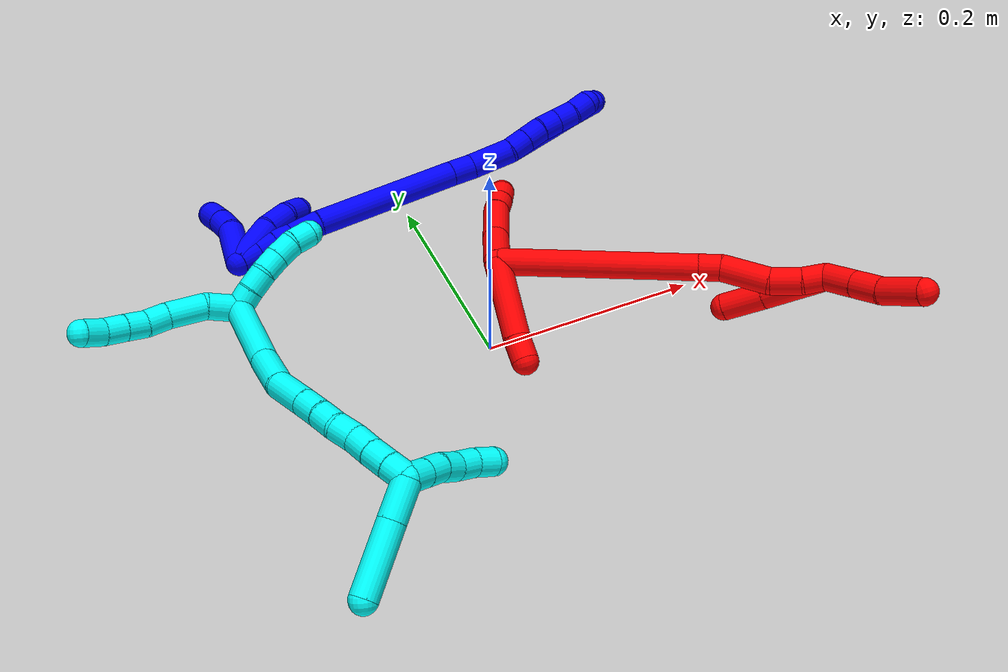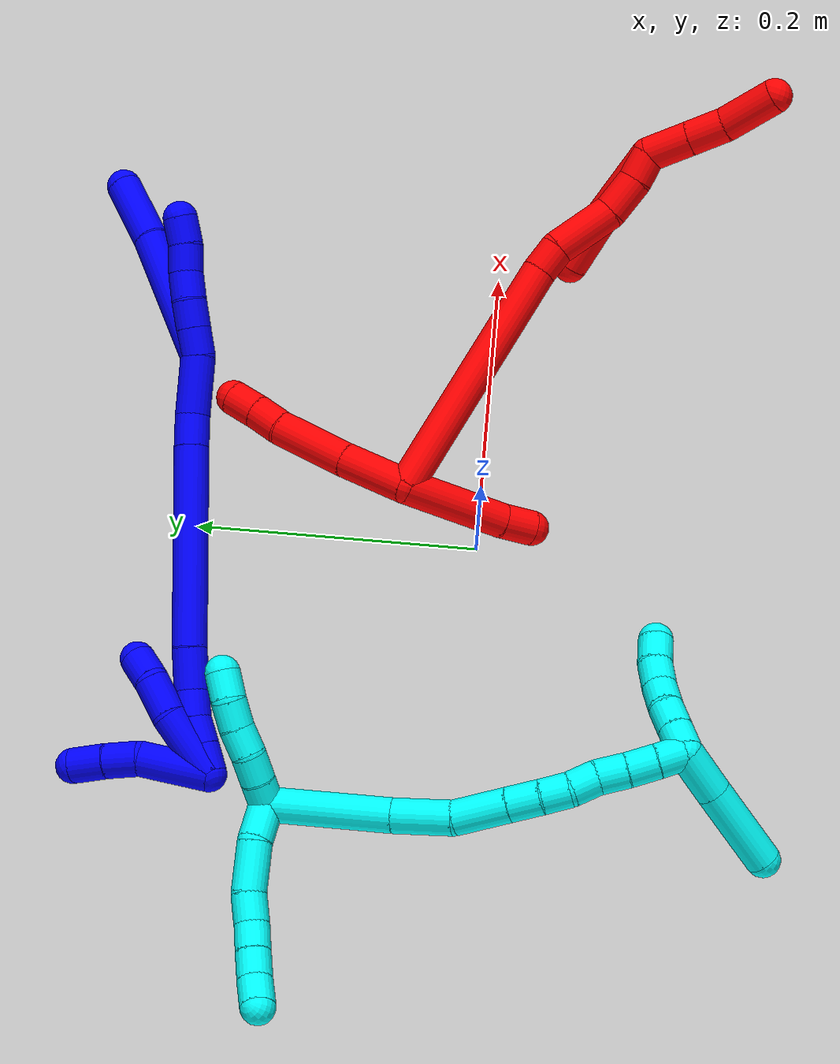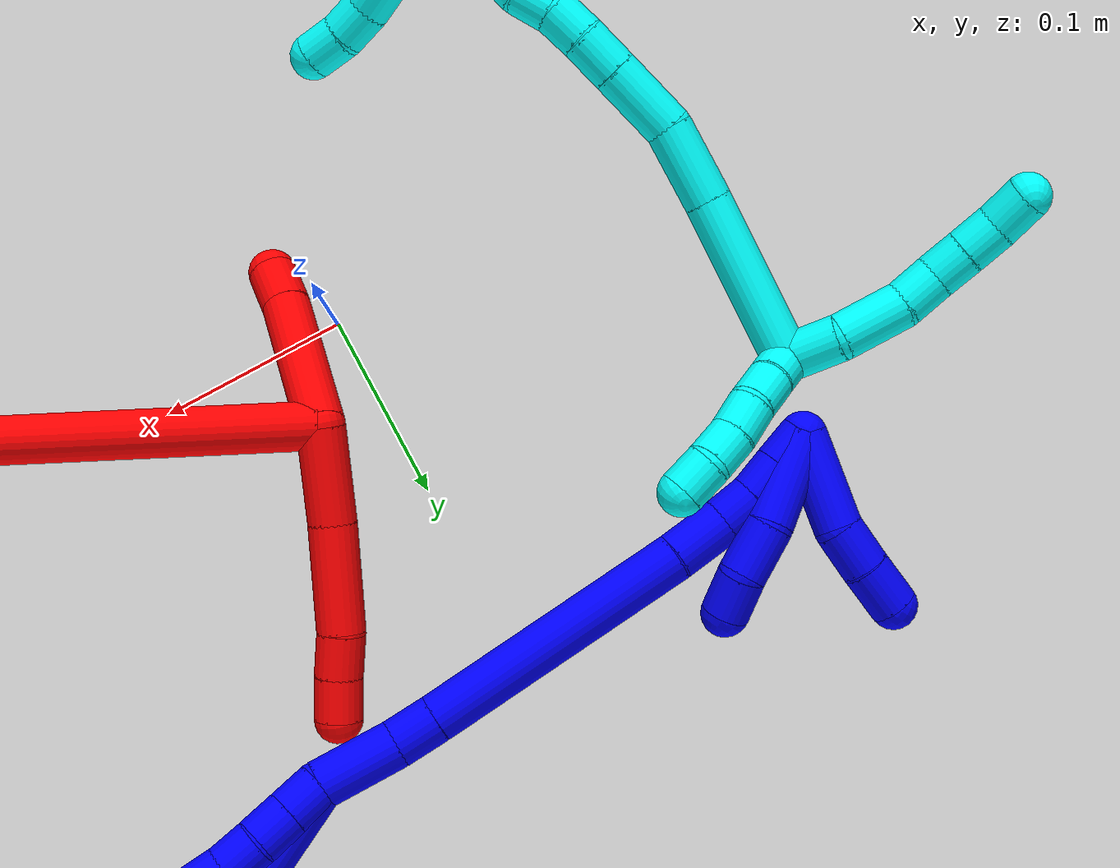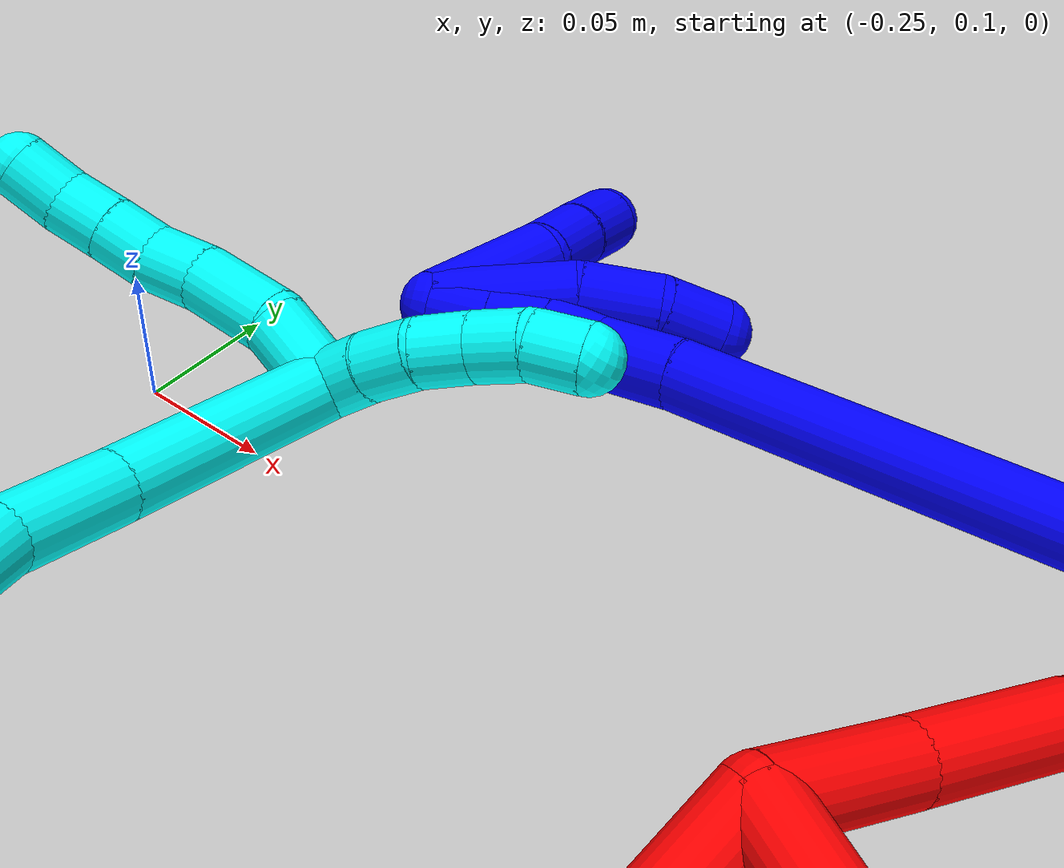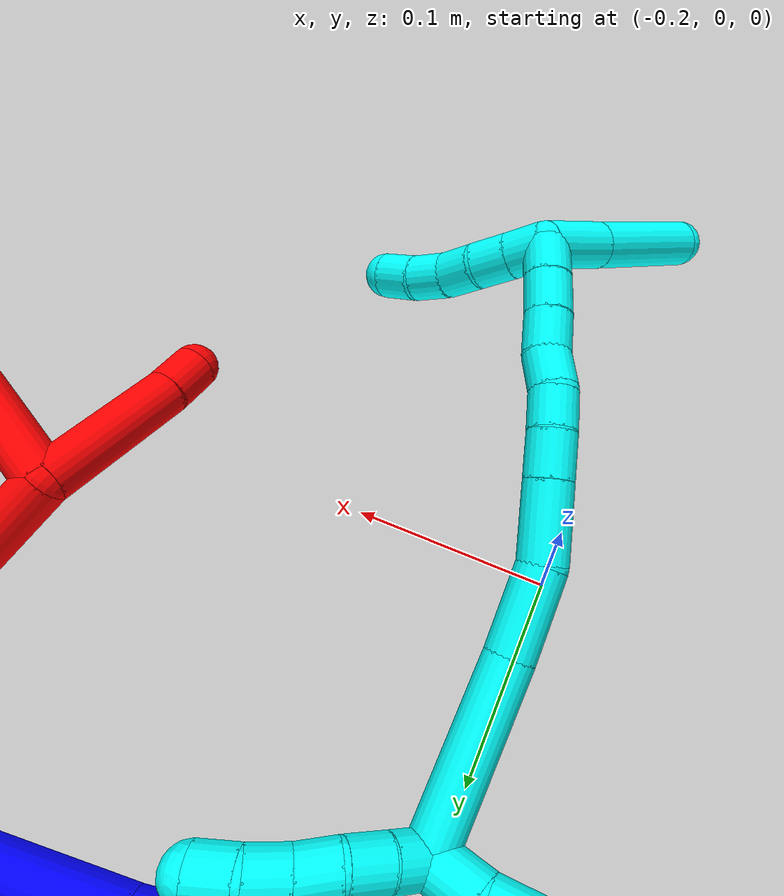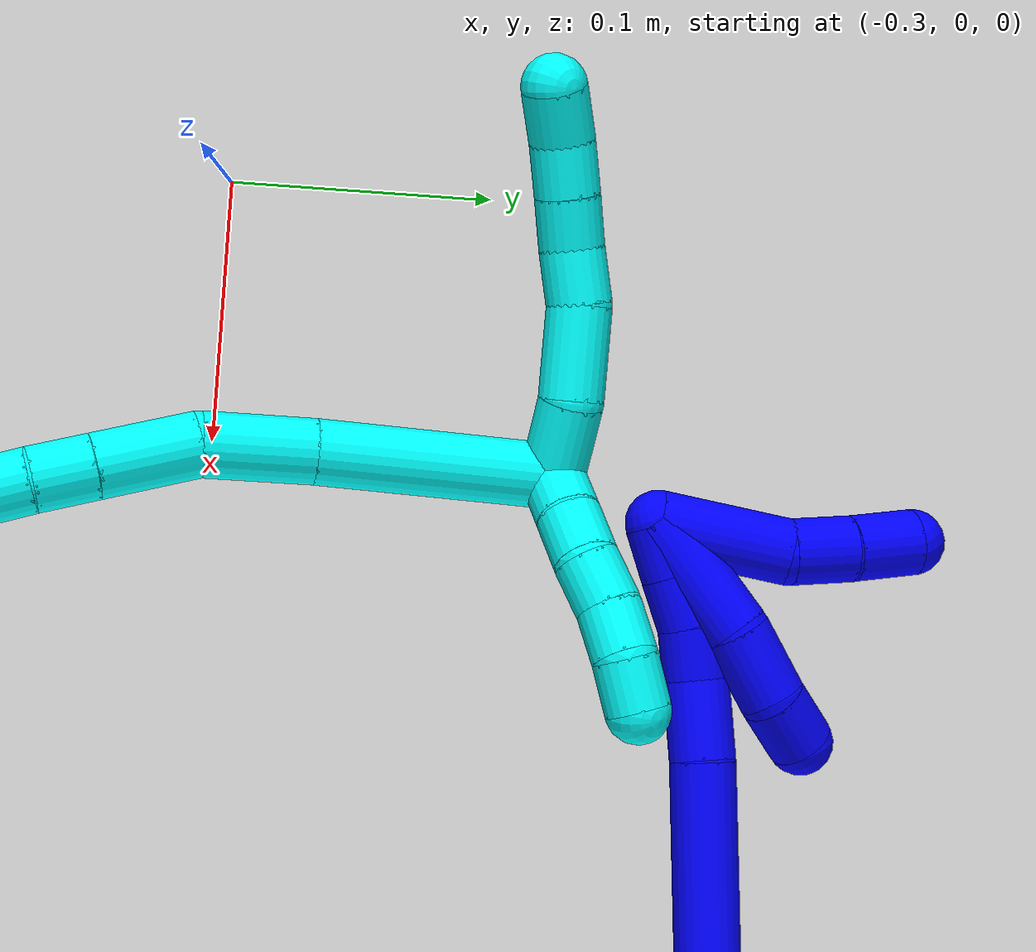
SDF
<sdf version="1.7">
 <world name="default">
  <plugin name="TubeGeneratorPlugin" filename="libtube_generator_plugin.so"/>
  <model name="photoneo_s_sensor">
   <static>1</static>
   <pose>0 0 2 1.57079 1.57079 3.14159</pose>
   <link name="link">
    <inertial><mass>0.1</mass></inertial>
    <sensor name="sensor" type="depth">
     <update_rate>30</update_rate>
     <camera>
      <horizontal_fov>1.22</horizontal_fov>
      <image><width>1920</width><height>1200</height><format>B8G8R8</format></image>
      <clip><near>0.1</near><far>4</far></clip>
      <depth_camera><output>points</output></depth_camera>
     </camera>
     <plugin name="camera_plugin" filename="libgazebo_ros_depth_camera.so">
      <baseline>0.2</baseline>
      <alwaysOn>1</alwaysOn>
      <updateRate>0.0</updateRate>
      <cameraName>camera_ir</cameraName>
      <imageTopicName>/camera/color/image_raw</imageTopicName>
      <cameraInfoTopicName>/camera/color/camera_info</cameraInfoTopicName>
      <depthImageTopicName>/camera/depth/image_raw</depthImageTopicName>
      <depthImageCameraInfoTopicName>/camera/depth/camera_info</depthImageCameraInfoTopicName>
      <pointCloudTopicName>/camera/depth/points</pointCloudTopicName>
      <frameName>fr_optical</frameName>
      <pointCloudCutoff>0.1</pointCloudCutoff>
      <pointCloudCutoffMax>2.0</pointCloudCutoffMax>
      <distortionK1>0</distortionK1>
      <distortionK2>0</distortionK2>
      <distortionK3>0</distortionK3>
      <distortionT1>0</distortionT1>
      <distortionT2>0</distortionT2>
      <CxPrime>0</CxPrime>
      <Cx>0</Cx>
      <Cy>0</Cy>
      <focalLength>0</focalLength>
      <hackBaseline>0</hackBaseline>
     </plugin>
    </sensor>
   </link>
  </model>
  <gravity>0 0 -9.8</gravity>
  <magnetic_field>6e-06 2.3e-05 -4.2e-05</magnetic_field>
  <atmosphere type="adiabatic"/>
  <physics name="default_physics" default="0" type="ode">
   <max_step_size>0.003</max_step_size>
   <real_time_factor>1</real_time_factor>
   <real_time_update_rate>1000</real_time_update_rate>
   <max_contacts>10000</max_contacts>
   <ode>
    <solver>
     <type>quick</type>
     <iters>100</iters>
     <sor>1.3</sor>
     <use_dynamic_moi_rescaling>0</use_dynamic_moi_rescaling>
    </solver>
    <constraints>
     <contact_max_correcting_vel>0</contact_max_correcting_vel>
     <contact_surface_layer>0.001</contact_surface_layer>
     <cfm>0</cfm>
     <erp>0.2</erp>
    </constraints>
   </ode>
  </physics>
  <scene><ambient>0.4 0.4 0.4 1</ambient><background>0.7 0.7 0.7 1</background><shadows>0</shadows></scene>
  <audio><device>default</device></audio>
  <spherical_coordinates>
   <surface_model>EARTH_WGS84</surface_model>
   <latitude_deg>0</latitude_deg>
   <longitude_deg>0</longitude_deg>
   <elevation>0</elevation>
   <heading_deg>0</heading_deg>
  </spherical_coordinates>
  <model name="bin">
   <static>1</static>
   <link name="bottom">
    <collision name="collision-bottom">
     <pose>0 0 -0.01 0 -0 0</pose>
     <geometry><box><size>0.8 0.6 0.02</size></box></geometry>
     <surface>
      <friction><ode><mu>100</mu><mu2>100</mu2></ode></friction>
      <contact><collide_bitmask>65535</collide_bitmask></contact>
     </surface>
    </collision>
   </link>
   <link name="west_wall">
    <collision name="collision-west_wall">
     <pose>-0.41 0 0.1 0 -0 0</pose>
     <geometry><box><size>0.02 0.6 0.2</size></box></geometry>
     <surface>
      <friction><ode><mu>100</mu><mu2>100</mu2></ode></friction>
      <contact><collide_bitmask>65535</collide_bitmask></contact>
     </surface>
    </collision>
   </link>
   <link name="east_wall">
    <collision name="collision-east_wall">
     <pose>0.41 0 0.1 0 -0 0</pose>
     <geometry><box><size>0.02 0.6 0.2</size></box></geometry>
     <surface>
      <friction><ode><mu>100</mu><mu2>100</mu2></ode></friction>
      <contact><collide_bitmask>65535</collide_bitmask></contact>
     </surface>
    </collision>
   </link>
   <link name="south_wall">
    <collision name="collision-south_wall">
     <pose>0 -0.31 0.1 0 -0 0</pose>
     <geometry><box><size>0.8 0.02 0.2</size></box></geometry>
     <surface>
      <friction><ode><mu>100</mu><mu2>100</mu2></ode></friction>
      <contact><collide_bitmask>65535</collide_bitmask></contact>
     </surface>
    </collision>
   </link>
   <link name="north_wall">
    <collision name="collision-north_wall">
     <pose>0 0.31 0.1 0 -0 0</pose>
     <geometry><box><size>0.8 0.02 0.2</size></box></geometry>
     <surface>
      <friction><ode><mu>100</mu><mu2>100</mu2></ode></friction>
      <contact><collide_bitmask>65535</collide_bitmask></contact>
     </surface>
    </collision>
   </link>
  </model>
  <model name="1">
   <static>0</static>
   <link name="1">
    <collision name="collision-cylinder-e_1_2_8">
     <pose>0.001028 -0.001355 -0.049775 3.11437 0.020641 1.2976</pose>
     <geometry><cylinder><radius>0.0125</radius><length>0.099608</length></cylinder></geometry>
     <surface>
      <friction><ode><mu>1.16</mu><mu2>1.16</mu2><slip1>0</slip1><slip2>0</slip2></ode></friction>
      <contact><ode><kp>1e+06</kp><kd>1</kd><max_vel>0</max_vel><min_depth>0.001</min_depth></ode></contact>
     </surface>
    </collision>
    <visual name="visual-cylinder-e_1_2_8">
     <pose>0.001028 -0.001355 -0.049775 3.11437 0.020641 1.2976</pose>
     <geometry><cylinder><radius>0.0125</radius><length>0.099608</length></cylinder></geometry>
     <material><ambient>0 0 1 1</ambient></material>
    </visual>
    <collision name="collision-cylinder-e_2_8_6">
     <pose>4.5e-05 -0.001469 -0.124635 -3.09215 -0.079874 2.0333</pose>
     <geometry><cylinder><radius>0.0125</radius><length>0.050392</length></cylinder></geometry>
     <surface>
      <friction><ode><mu>1.16</mu><mu2>1.16</mu2><slip1>0</slip1><slip2>0</slip2></ode></friction>
      <contact><ode><kp>1e+06</kp><kd>1</kd><max_vel>0</max_vel><min_depth>0.001</min_depth></ode></contact>
     </surface>
    </collision>
    <visual name="visual-cylinder-e_2_8_6">
     <pose>4.5e-05 -0.001469 -0.124635 -3.09215 -0.079874 2.0333</pose>
     <geometry><cylinder><radius>0.0125</radius><length>0.050392</length></cylinder></geometry>
     <material><ambient>0 0 1 1</ambient></material>
    </visual>
    <collision name="collision-cylinder-e_1_2_9">
     <pose>0.003402 -0.002503 -0.009064 2.87213 0.347146 1.82536</pose>
     <geometry><cylinder><radius>0.0125</radius><length>0.02</length></cylinder></geometry>
     <surface>
      <friction><ode><mu>1.16</mu><mu2>1.16</mu2><slip1>0</slip1><slip2>0</slip2></ode></friction>
      <contact><ode><kp>1e+06</kp><kd>1</kd><max_vel>0</max_vel><min_depth>0.001</min_depth></ode></contact>
     </surface>
    </collision>
    <visual name="visual-cylinder-e_1_2_9">
     <pose>0.003402 -0.002503 -0.009064 2.87213 0.347146 1.82536</pose>
     <geometry><cylinder><radius>0.0125</radius><length>0.02</length></cylinder></geometry>
     <material><ambient>0 0 1 1</ambient></material>
    </visual>
    <collision name="collision-cylinder-e_2_9_10">
     <pose>0.01017 -0.007563 -0.027191 2.86663 0.343254 1.79432</pose>
     <geometry><cylinder><radius>0.0125</radius><length>0.02</length></cylinder></geometry>
     <surface>
      <friction><ode><mu>1.16</mu><mu2>1.16</mu2><slip1>0</slip1><slip2>0</slip2></ode></friction>
      <contact><ode><kp>1e+06</kp><kd>1</kd><max_vel>0</max_vel><min_depth>0.001</min_depth></ode></contact>
     </surface>
    </collision>
    <visual name="visual-cylinder-e_2_9_10">
     <pose>0.01017 -0.007563 -0.027191 2.86663 0.343254 1.79432</pose>
     <geometry><cylinder><radius>0.0125</radius><length>0.02</length></cylinder></geometry>
     <material><ambient>0 0 1 1</ambient></material>
    </visual>
    <collision name="collision-cylinder-e_3_10_11">
     <pose>0.01549 -0.012984 -0.045634 2.84525 0.196704 1.1682</pose>
     <geometry><cylinder><radius>0.0125</radius><length>0.02</length></cylinder></geometry>
     <surface>
      <friction><ode><mu>1.16</mu><mu2>1.16</mu2><slip1>0</slip1><slip2>0</slip2></ode></friction>
      <contact><ode><kp>1e+06</kp><kd>1</kd><max_vel>0</max_vel><min_depth>0.001</min_depth></ode></contact>
     </surface>
    </collision>
    <visual name="visual-cylinder-e_3_10_11">
     <pose>0.01549 -0.012984 -0.045634 2.84525 0.196704 1.1682</pose>
     <geometry><cylinder><radius>0.0125</radius><length>0.02</length></cylinder></geometry>
     <material><ambient>0 0 1 1</ambient></material>
    </visual>
    <collision name="collision-cylinder-e_4_11_12">
     <pose>0.020265 -0.019809 -0.063752 2.71603 0.28599 1.17564</pose>
     <geometry><cylinder><radius>0.0125</radius><length>0.02</length></cylinder></geometry>
     <surface>
      <friction><ode><mu>1.16</mu><mu2>1.16</mu2><slip1>0</slip1><slip2>0</slip2></ode></friction>
      <contact><ode><kp>1e+06</kp><kd>1</kd><max_vel>0</max_vel><min_depth>0.001</min_depth></ode></contact>
     </surface>
    </collision>
    <visual name="visual-cylinder-e_4_11_12">
     <pose>0.020265 -0.019809 -0.063752 2.71603 0.28599 1.17564</pose>
     <geometry><cylinder><radius>0.0125</radius><length>0.02</length></cylinder></geometry>
     <material><ambient>0 0 1 1</ambient></material>
    </visual>
    <collision name="collision-cylinder-e_5_12_5">
     <pose>0.026112 -0.025903 -0.081779 2.91583 0.307366 1.87806</pose>
     <geometry><cylinder><radius>0.0125</radius><length>0.02</length></cylinder></geometry>
     <surface>
      <friction><ode><mu>1.16</mu><mu2>1.16</mu2><slip1>0</slip1><slip2>0</slip2></ode></friction>
      <contact><ode><kp>1e+06</kp><kd>1</kd><max_vel>0</max_vel><min_depth>0.001</min_depth></ode></contact>
     </surface>
    </collision>
    <visual name="visual-cylinder-e_5_12_5">
     <pose>0.026112 -0.025903 -0.081779 2.91583 0.307366 1.87806</pose>
     <geometry><cylinder><radius>0.0125</radius><length>0.02</length></cylinder></geometry>
     <material><ambient>0 0 1 1</ambient></material>
    </visual>
    <collision name="collision-cylinder-e_1_2_13">
     <pose>-0.005703 0.010234 0.017705 -0.52411 -0.271969 0.073369</pose>
     <geometry><cylinder><radius>0.0125</radius><length>0.042461</length></cylinder></geometry>
     <surface>
      <friction><ode><mu>1.16</mu><mu2>1.16</mu2><slip1>0</slip1><slip2>0</slip2></ode></friction>
      <contact><ode><kp>1e+06</kp><kd>1</kd><max_vel>0</max_vel><min_depth>0.001</min_depth></ode></contact>
     </surface>
    </collision>
    <visual name="visual-cylinder-e_1_2_13">
     <pose>-0.005703 0.010234 0.017705 -0.52411 -0.271969 0.073369</pose>
     <geometry><cylinder><radius>0.0125</radius><length>0.042461</length></cylinder></geometry>
     <material><ambient>0 0 1 1</ambient></material>
    </visual>
    <collision name="collision-cylinder-e_2_13_14">
     <pose>-0.01308 0.025375 0.045831 -0.440034 -0.144268 0.032317</pose>
     <geometry><cylinder><radius>0.0125</radius><length>0.023278</length></cylinder></geometry>
     <surface>
      <friction><ode><mu>1.16</mu><mu2>1.16</mu2><slip1>0</slip1><slip2>0</slip2></ode></friction>
      <contact><ode><kp>1e+06</kp><kd>1</kd><max_vel>0</max_vel><min_depth>0.001</min_depth></ode></contact>
     </surface>
    </collision>
    <visual name="visual-cylinder-e_2_13_14">
     <pose>-0.01308 0.025375 0.045831 -0.440034 -0.144268 0.032317</pose>
     <geometry><cylinder><radius>0.0125</radius><length>0.023278</length></cylinder></geometry>
     <material><ambient>0 0 1 1</ambient></material>
    </visual>
    <collision name="collision-cylinder-e_3_14_15">
     <pose>-0.02563 0.058857 0.121288 -0.413996 -0.151933 0.031966</pose>
     <geometry><cylinder><radius>0.0125</radius><length>0.143729</length></cylinder></geometry>
     <surface>
      <friction><ode><mu>1.16</mu><mu2>1.16</mu2><slip1>0</slip1><slip2>0</slip2></ode></friction>
      <contact><ode><kp>1e+06</kp><kd>1</kd><max_vel>0</max_vel><min_depth>0.001</min_depth></ode></contact>
     </surface>
    </collision>
    <visual name="visual-cylinder-e_3_14_15">
     <pose>-0.02563 0.058857 0.121288 -0.413996 -0.151933 0.031966</pose>
     <geometry><cylinder><radius>0.0125</radius><length>0.143729</length></cylinder></geometry>
     <material><ambient>0 0 1 1</ambient></material>
    </visual>
    <collision name="collision-cylinder-e_4_15_16">
     <pose>-0.039924 0.092764 0.200116 -0.368845 -0.22716 0.042552</pose>
     <geometry><cylinder><radius>0.0125</radius><length>0.030353</length></cylinder></geometry>
     <surface>
      <friction><ode><mu>1.16</mu><mu2>1.16</mu2><slip1>0</slip1><slip2>0</slip2></ode></friction>
      <contact><ode><kp>1e+06</kp><kd>1</kd><max_vel>0</max_vel><min_depth>0.001</min_depth></ode></contact>
     </surface>
    </collision>
    <visual name="visual-cylinder-e_4_15_16">
     <pose>-0.039924 0.092764 0.200116 -0.368845 -0.22716 0.042552</pose>
     <geometry><cylinder><radius>0.0125</radius><length>0.030353</length></cylinder></geometry>
     <material><ambient>0 0 1 1</ambient></material>
    </visual>
    <collision name="collision-cylinder-e_5_16_17">
     <pose>-0.044107 0.101235 0.223404 -0.31929 -0.076274 0.012287</pose>
     <geometry><cylinder><radius>0.0125</radius><length>0.020062</length></cylinder></geometry>
     <surface>
      <friction><ode><mu>1.16</mu><mu2>1.16</mu2><slip1>0</slip1><slip2>0</slip2></ode></friction>
      <contact><ode><kp>1e+06</kp><kd>1</kd><max_vel>0</max_vel><min_depth>0.001</min_depth></ode></contact>
     </surface>
    </collision>
    <visual name="visual-cylinder-e_5_16_17">
     <pose>-0.044107 0.101235 0.223404 -0.31929 -0.076274 0.012287</pose>
     <geometry><cylinder><radius>0.0125</radius><length>0.020062</length></cylinder></geometry>
     <material><ambient>0 0 1 1</ambient></material>
    </visual>
    <collision name="collision-cylinder-e_6_17_18">
     <pose>-0.045968 0.105504 0.242796 -0.113635 -0.109735 0.006248</pose>
     <geometry><cylinder><radius>0.0125</radius><length>0.02004</length></cylinder></geometry>
     <surface>
      <friction><ode><mu>1.16</mu><mu2>1.16</mu2><slip1>0</slip1><slip2>0</slip2></ode></friction>
      <contact><ode><kp>1e+06</kp><kd>1</kd><max_vel>0</max_vel><min_depth>0.001</min_depth></ode></contact>
     </surface>
    </collision>
    <visual name="visual-cylinder-e_6_17_18">
     <pose>-0.045968 0.105504 0.242796 -0.113635 -0.109735 0.006248</pose>
     <geometry><cylinder><radius>0.0125</radius><length>0.02004</length></cylinder></geometry>
     <material><ambient>0 0 1 1</ambient></material>
    </visual>
    <collision name="collision-cylinder-e_7_18_1">
     <pose>-0.048131 0.107903 0.262592 -0.127551 -0.106344 0.006798</pose>
     <geometry><cylinder><radius>0.0125</radius><length>0.020076</length></cylinder></geometry>
     <surface>
      <friction><ode><mu>1.16</mu><mu2>1.16</mu2><slip1>0</slip1><slip2>0</slip2></ode></friction>
      <contact><ode><kp>1e+06</kp><kd>1</kd><max_vel>0</max_vel><min_depth>0.001</min_depth></ode></contact>
     </surface>
    </collision>
    <visual name="visual-cylinder-e_7_18_1">
     <pose>-0.048131 0.107903 0.262592 -0.127551 -0.106344 0.006798</pose>
     <geometry><cylinder><radius>0.0125</radius><length>0.020076</length></cylinder></geometry>
     <material><ambient>0 0 1 1</ambient></material>
    </visual>
    <collision name="collision-cylinder-e_1_1_19">
     <pose>-0.043335 0.113907 0.248927 -2.94333 0.239182 -1.75883</pose>
     <geometry><cylinder><radius>0.0125</radius><length>0.049481</length></cylinder></geometry>
     <surface>
      <friction><ode><mu>1.16</mu><mu2>1.16</mu2><slip1>0</slip1><slip2>0</slip2></ode></friction>
      <contact><ode><kp>1e+06</kp><kd>1</kd><max_vel>0</max_vel><min_depth>0.001</min_depth></ode></contact>
     </surface>
    </collision>
    <visual name="visual-cylinder-e_1_1_19">
     <pose>-0.043335 0.113907 0.248927 -2.94333 0.239182 -1.75883</pose>
     <geometry><cylinder><radius>0.0125</radius><length>0.049481</length></cylinder></geometry>
     <material><ambient>0 0 1 1</ambient></material>
    </visual>
    <collision name="collision-cylinder-e_2_19_20">
     <pose>-0.036807 0.119619 0.211224 -3.07253 0.047071 -1.19624</pose>
     <geometry><cylinder><radius>0.0125</radius><length>0.028374</length></cylinder></geometry>
     <surface>
      <friction><ode><mu>1.16</mu><mu2>1.16</mu2><slip1>0</slip1><slip2>0</slip2></ode></friction>
      <contact><ode><kp>1e+06</kp><kd>1</kd><max_vel>0</max_vel><min_depth>0.001</min_depth></ode></contact>
     </surface>
    </collision>
    <visual name="visual-cylinder-e_2_19_20">
     <pose>-0.036807 0.119619 0.211224 -3.07253 0.047071 -1.19624</pose>
     <geometry><cylinder><radius>0.0125</radius><length>0.028374</length></cylinder></geometry>
     <material><ambient>0 0 1 1</ambient></material>
    </visual>
    <collision name="collision-cylinder-e_3_20_4">
     <pose>-0.03897 0.12239 0.186533 -2.97333 -0.258525 1.99059</pose>
     <geometry><cylinder><radius>0.0125</radius><length>0.022145</length></cylinder></geometry>
     <surface>
      <friction><ode><mu>1.16</mu><mu2>1.16</mu2><slip1>0</slip1><slip2>0</slip2></ode></friction>
      <contact><ode><kp>1e+06</kp><kd>1</kd><max_vel>0</max_vel><min_depth>0.001</min_depth></ode></contact>
     </surface>
    </collision>
    <visual name="visual-cylinder-e_3_20_4">
     <pose>-0.03897 0.12239 0.186533 -2.97333 -0.258525 1.99059</pose>
     <geometry><cylinder><radius>0.0125</radius><length>0.022145</length></cylinder></geometry>
     <material><ambient>0 0 1 1</ambient></material>
    </visual>
    <collision name="collision-cylinder-e_1_1_21">
     <pose>-0.047489 0.129218 0.25759 -2.21007 0.068276 -0.135676</pose>
     <geometry><cylinder><radius>0.0125</radius><length>0.050072</length></cylinder></geometry>
     <surface>
      <friction><ode><mu>1.16</mu><mu2>1.16</mu2><slip1>0</slip1><slip2>0</slip2></ode></friction>
      <contact><ode><kp>1e+06</kp><kd>1</kd><max_vel>0</max_vel><min_depth>0.001</min_depth></ode></contact>
     </surface>
    </collision>
    <visual name="visual-cylinder-e_1_1_21">
     <pose>-0.047489 0.129218 0.25759 -2.21007 0.068276 -0.135676</pose>
     <geometry><cylinder><radius>0.0125</radius><length>0.050072</length></cylinder></geometry>
     <material><ambient>0 0 1 1</ambient></material>
    </visual>
    <collision name="collision-cylinder-e_2_21_22">
     <pose>-0.047354 0.160436 0.238022 -1.96642 -0.129222 0.193671</pose>
     <geometry><cylinder><radius>0.0125</radius><length>0.024419</length></cylinder></geometry>
     <surface>
      <friction><ode><mu>1.16</mu><mu2>1.16</mu2><slip1>0</slip1><slip2>0</slip2></ode></friction>
      <contact><ode><kp>1e+06</kp><kd>1</kd><max_vel>0</max_vel><min_depth>0.001</min_depth></ode></contact>
     </surface>
    </collision>
    <visual name="visual-cylinder-e_2_21_22">
     <pose>-0.047354 0.160436 0.238022 -1.96642 -0.129222 0.193671</pose>
     <geometry><cylinder><radius>0.0125</radius><length>0.024419</length></cylinder></geometry>
     <material><ambient>0 0 1 1</ambient></material>
    </visual>
    <collision name="collision-cylinder-e_3_22_3">
     <pose>-0.05162 0.183286 0.22899 -1.9286 -0.212736 0.305425</pose>
     <geometry><cylinder><radius>0.0125</radius><length>0.025508</length></cylinder></geometry>
     <surface>
      <friction><ode><mu>1.16</mu><mu2>1.16</mu2><slip1>0</slip1><slip2>0</slip2></ode></friction>
      <contact><ode><kp>1e+06</kp><kd>1</kd><max_vel>0</max_vel><min_depth>0.001</min_depth></ode></contact>
     </surface>
    </collision>
    <visual name="visual-cylinder-e_3_22_3">
     <pose>-0.05162 0.183286 0.22899 -1.9286 -0.212736 0.305425</pose>
     <geometry><cylinder><radius>0.0125</radius><length>0.025508</length></cylinder></geometry>
     <material><ambient>0 0 1 1</ambient></material>
    </visual>
    <collision name="collision-sphere-3">
     <pose>-0.054313 0.194963 0.224624 0 -0 0</pose>
     <geometry><sphere><radius>0.0125</radius></sphere></geometry>
     <surface>
      <friction><ode><mu>1.16</mu><mu2>1.16</mu2><slip1>0</slip1><slip2>0</slip2></ode></friction>
      <contact><ode><kp>1e+06</kp><kd>1</kd><max_vel>0</max_vel><min_depth>0.001</min_depth></ode></contact>
     </surface>
    </collision>
    <visual name="visual-sphere-3">
     <pose>-0.054313 0.194963 0.224624 0 -0 0</pose>
     <geometry><sphere><radius>0.0125</radius></sphere></geometry>
     <material><ambient>0 0 1 1</ambient></material>
    </visual>
    <collision name="collision-sphere-22">
     <pose>-0.048927 0.171609 0.233356 0 -0 0</pose>
     <geometry><sphere><radius>0.0125</radius></sphere></geometry>
     <surface>
      <friction><ode><mu>1.16</mu><mu2>1.16</mu2><slip1>0</slip1><slip2>0</slip2></ode></friction>
      <contact><ode><kp>1e+06</kp><kd>1</kd><max_vel>0</max_vel><min_depth>0.001</min_depth></ode></contact>
     </surface>
    </collision>
    <visual name="visual-sphere-22">
     <pose>-0.048927 0.171609 0.233356 0 -0 0</pose>
     <geometry><sphere><radius>0.0125</radius></sphere></geometry>
     <material><ambient>0 0 1 1</ambient></material>
    </visual>
    <collision name="collision-sphere-21">
     <pose>-0.04578 0.149263 0.242688 0 -0 0</pose>
     <geometry><sphere><radius>0.0125</radius></sphere></geometry>
     <surface>
      <friction><ode><mu>1.16</mu><mu2>1.16</mu2><slip1>0</slip1><slip2>0</slip2></ode></friction>
      <contact><ode><kp>1e+06</kp><kd>1</kd><max_vel>0</max_vel><min_depth>0.001</min_depth></ode></contact>
     </surface>
    </collision>
    <visual name="visual-sphere-21">
     <pose>-0.04578 0.149263 0.242688 0 -0 0</pose>
     <geometry><sphere><radius>0.0125</radius></sphere></geometry>
     <material><ambient>0 0 1 1</ambient></material>
    </visual>
    <collision name="collision-sphere-4">
     <pose>-0.041801 0.124182 0.17598 0 -0 0</pose>
     <geometry><sphere><radius>0.0125</radius></sphere></geometry>
     <surface>
      <friction><ode><mu>1.16</mu><mu2>1.16</mu2><slip1>0</slip1><slip2>0</slip2></ode></friction>
      <contact><ode><kp>1e+06</kp><kd>1</kd><max_vel>0</max_vel><min_depth>0.001</min_depth></ode></contact>
     </surface>
    </collision>
    <visual name="visual-sphere-4">
     <pose>-0.041801 0.124182 0.17598 0 -0 0</pose>
     <geometry><sphere><radius>0.0125</radius></sphere></geometry>
     <material><ambient>0 0 1 1</ambient></material>
    </visual>
    <collision name="collision-sphere-20">
     <pose>-0.036139 0.120597 0.197087 0 -0 0</pose>
     <geometry><sphere><radius>0.0125</radius></sphere></geometry>
     <surface>
      <friction><ode><mu>1.16</mu><mu2>1.16</mu2><slip1>0</slip1><slip2>0</slip2></ode></friction>
      <contact><ode><kp>1e+06</kp><kd>1</kd><max_vel>0</max_vel><min_depth>0.001</min_depth></ode></contact>
     </surface>
    </collision>
    <visual name="visual-sphere-20">
     <pose>-0.036139 0.120597 0.197087 0 -0 0</pose>
     <geometry><sphere><radius>0.0125</radius></sphere></geometry>
     <material><ambient>0 0 1 1</ambient></material>
    </visual>
    <collision name="collision-sphere-11">
     <pose>0.017444 -0.015848 -0.055013 0 -0 0</pose>
     <geometry><sphere><radius>0.0125</radius></sphere></geometry>
     <surface>
      <friction><ode><mu>1.16</mu><mu2>1.16</mu2><slip1>0</slip1><slip2>0</slip2></ode></friction>
      <contact><ode><kp>1e+06</kp><kd>1</kd><max_vel>0</max_vel><min_depth>0.001</min_depth></ode></contact>
     </surface>
    </collision>
    <visual name="visual-sphere-11">
     <pose>0.017444 -0.015848 -0.055013 0 -0 0</pose>
     <geometry><sphere><radius>0.0125</radius></sphere></geometry>
     <material><ambient>0 0 1 1</ambient></material>
    </visual>
    <collision name="collision-sphere-10">
     <pose>0.013535 -0.01012 -0.036254 0 -0 0</pose>
     <geometry><sphere><radius>0.0125</radius></sphere></geometry>
     <surface>
      <friction><ode><mu>1.16</mu><mu2>1.16</mu2><slip1>0</slip1><slip2>0</slip2></ode></friction>
      <contact><ode><kp>1e+06</kp><kd>1</kd><max_vel>0</max_vel><min_depth>0.001</min_depth></ode></contact>
     </surface>
    </collision>
    <visual name="visual-sphere-10">
     <pose>0.013535 -0.01012 -0.036254 0 -0 0</pose>
     <geometry><sphere><radius>0.0125</radius></sphere></geometry>
     <material><ambient>0 0 1 1</ambient></material>
    </visual>
    <collision name="collision-sphere-6">
     <pose>-0.001965 -0.000228 -0.14972 0 -0 0</pose>
     <geometry><sphere><radius>0.0125</radius></sphere></geometry>
     <surface>
      <friction><ode><mu>1.16</mu><mu2>1.16</mu2><slip1>0</slip1><slip2>0</slip2></ode></friction>
      <contact><ode><kp>1e+06</kp><kd>1</kd><max_vel>0</max_vel><min_depth>0.001</min_depth></ode></contact>
     </surface>
    </collision>
    <visual name="visual-sphere-6">
     <pose>-0.001965 -0.000228 -0.14972 0 -0 0</pose>
     <geometry><sphere><radius>0.0125</radius></sphere></geometry>
     <material><ambient>0 0 1 1</ambient></material>
    </visual>
    <collision name="collision-sphere-9">
     <pose>0.006804 -0.005007 -0.018128 0 -0 0</pose>
     <geometry><sphere><radius>0.0125</radius></sphere></geometry>
     <surface>
      <friction><ode><mu>1.16</mu><mu2>1.16</mu2><slip1>0</slip1><slip2>0</slip2></ode></friction>
      <contact><ode><kp>1e+06</kp><kd>1</kd><max_vel>0</max_vel><min_depth>0.001</min_depth></ode></contact>
     </surface>
    </collision>
    <visual name="visual-sphere-9">
     <pose>0.006804 -0.005007 -0.018128 0 -0 0</pose>
     <geometry><sphere><radius>0.0125</radius></sphere></geometry>
     <material><ambient>0 0 1 1</ambient></material>
    </visual>
    <collision name="collision-sphere-2">
     <geometry><sphere><radius>0.0125</radius></sphere></geometry>
     <surface>
      <friction><ode><mu>1.16</mu><mu2>1.16</mu2><slip1>0</slip1><slip2>0</slip2></ode></friction>
      <contact><ode><kp>1e+06</kp><kd>1</kd><max_vel>0</max_vel><min_depth>0.001</min_depth></ode></contact>
     </surface>
    </collision>
    <visual name="visual-sphere-2">
     <geometry><sphere><radius>0.0125</radius></sphere></geometry>
     <material><ambient>0 0 1 1</ambient></material>
    </visual>
    <collision name="collision-sphere-19">
     <pose>-0.037474 0.118641 0.225362 0 -0 0</pose>
     <geometry><sphere><radius>0.0125</radius></sphere></geometry>
     <surface>
      <friction><ode><mu>1.16</mu><mu2>1.16</mu2><slip1>0</slip1><slip2>0</slip2></ode></friction>
      <contact><ode><kp>1e+06</kp><kd>1</kd><max_vel>0</max_vel><min_depth>0.001</min_depth></ode></contact>
     </surface>
    </collision>
    <visual name="visual-sphere-19">
     <pose>-0.037474 0.118641 0.225362 0 -0 0</pose>
     <geometry><sphere><radius>0.0125</radius></sphere></geometry>
     <material><ambient>0 0 1 1</ambient></material>
    </visual>
    <collision name="collision-sphere-8">
     <pose>0.002056 -0.00271 -0.09955 0 -0 0</pose>
     <geometry><sphere><radius>0.0125</radius></sphere></geometry>
     <surface>
      <friction><ode><mu>1.16</mu><mu2>1.16</mu2><slip1>0</slip1><slip2>0</slip2></ode></friction>
      <contact><ode><kp>1e+06</kp><kd>1</kd><max_vel>0</max_vel><min_depth>0.001</min_depth></ode></contact>
     </surface>
    </collision>
    <visual name="visual-sphere-8">
     <pose>0.002056 -0.00271 -0.09955 0 -0 0</pose>
     <geometry><sphere><radius>0.0125</radius></sphere></geometry>
     <material><ambient>0 0 1 1</ambient></material>
    </visual>
    <collision name="collision-sphere-12">
     <pose>0.023086 -0.023769 -0.07249 0 -0 0</pose>
     <geometry><sphere><radius>0.0125</radius></sphere></geometry>
     <surface>
      <friction><ode><mu>1.16</mu><mu2>1.16</mu2><slip1>0</slip1><slip2>0</slip2></ode></friction>
      <contact><ode><kp>1e+06</kp><kd>1</kd><max_vel>0</max_vel><min_depth>0.001</min_depth></ode></contact>
     </surface>
    </collision>
    <visual name="visual-sphere-12">
     <pose>0.023086 -0.023769 -0.07249 0 -0 0</pose>
     <geometry><sphere><radius>0.0125</radius></sphere></geometry>
     <material><ambient>0 0 1 1</ambient></material>
    </visual>
    <collision name="collision-sphere-5">
     <pose>0.029137 -0.028036 -0.091069 0 -0 0</pose>
     <geometry><sphere><radius>0.0125</radius></sphere></geometry>
     <surface>
      <friction><ode><mu>1.16</mu><mu2>1.16</mu2><slip1>0</slip1><slip2>0</slip2></ode></friction>
      <contact><ode><kp>1e+06</kp><kd>1</kd><max_vel>0</max_vel><min_depth>0.001</min_depth></ode></contact>
     </surface>
    </collision>
    <visual name="visual-sphere-5">
     <pose>0.029137 -0.028036 -0.091069 0 -0 0</pose>
     <geometry><sphere><radius>0.0125</radius></sphere></geometry>
     <material><ambient>0 0 1 1</ambient></material>
    </visual>
    <collision name="collision-sphere-13">
     <pose>-0.011406 0.020468 0.035411 0 -0 0</pose>
     <geometry><sphere><radius>0.0125</radius></sphere></geometry>
     <surface>
      <friction><ode><mu>1.16</mu><mu2>1.16</mu2><slip1>0</slip1><slip2>0</slip2></ode></friction>
      <contact><ode><kp>1e+06</kp><kd>1</kd><max_vel>0</max_vel><min_depth>0.001</min_depth></ode></contact>
     </surface>
    </collision>
    <visual name="visual-sphere-13">
     <pose>-0.011406 0.020468 0.035411 0 -0 0</pose>
     <geometry><sphere><radius>0.0125</radius></sphere></geometry>
     <material><ambient>0 0 1 1</ambient></material>
    </visual>
    <collision name="collision-sphere-14">
     <pose>-0.014753 0.030281 0.056252 0 -0 0</pose>
     <geometry><sphere><radius>0.0125</radius></sphere></geometry>
     <surface>
      <friction><ode><mu>1.16</mu><mu2>1.16</mu2><slip1>0</slip1><slip2>0</slip2></ode></friction>
      <contact><ode><kp>1e+06</kp><kd>1</kd><max_vel>0</max_vel><min_depth>0.001</min_depth></ode></contact>
     </surface>
    </collision>
    <visual name="visual-sphere-14">
     <pose>-0.014753 0.030281 0.056252 0 -0 0</pose>
     <geometry><sphere><radius>0.0125</radius></sphere></geometry>
     <material><ambient>0 0 1 1</ambient></material>
    </visual>
    <collision name="collision-sphere-15">
     <pose>-0.036506 0.087433 0.186324 0 -0 0</pose>
     <geometry><sphere><radius>0.0125</radius></sphere></geometry>
     <surface>
      <friction><ode><mu>1.16</mu><mu2>1.16</mu2><slip1>0</slip1><slip2>0</slip2></ode></friction>
      <contact><ode><kp>1e+06</kp><kd>1</kd><max_vel>0</max_vel><min_depth>0.001</min_depth></ode></contact>
     </surface>
    </collision>
    <visual name="visual-sphere-15">
     <pose>-0.036506 0.087433 0.186324 0 -0 0</pose>
     <geometry><sphere><radius>0.0125</radius></sphere></geometry>
     <material><ambient>0 0 1 1</ambient></material>
    </visual>
    <collision name="collision-sphere-16">
     <pose>-0.043342 0.098096 0.213908 0 -0 0</pose>
     <geometry><sphere><radius>0.0125</radius></sphere></geometry>
     <surface>
      <friction><ode><mu>1.16</mu><mu2>1.16</mu2><slip1>0</slip1><slip2>0</slip2></ode></friction>
      <contact><ode><kp>1e+06</kp><kd>1</kd><max_vel>0</max_vel><min_depth>0.001</min_depth></ode></contact>
     </surface>
    </collision>
    <visual name="visual-sphere-16">
     <pose>-0.043342 0.098096 0.213908 0 -0 0</pose>
     <geometry><sphere><radius>0.0125</radius></sphere></geometry>
     <material><ambient>0 0 1 1</ambient></material>
    </visual>
    <collision name="collision-sphere-17">
     <pose>-0.044871 0.104375 0.232901 0 -0 0</pose>
     <geometry><sphere><radius>0.0125</radius></sphere></geometry>
     <surface>
      <friction><ode><mu>1.16</mu><mu2>1.16</mu2><slip1>0</slip1><slip2>0</slip2></ode></friction>
      <contact><ode><kp>1e+06</kp><kd>1</kd><max_vel>0</max_vel><min_depth>0.001</min_depth></ode></contact>
     </surface>
    </collision>
    <visual name="visual-sphere-17">
     <pose>-0.044871 0.104375 0.232901 0 -0 0</pose>
     <geometry><sphere><radius>0.0125</radius></sphere></geometry>
     <material><ambient>0 0 1 1</ambient></material>
    </visual>
    <collision name="collision-sphere-18">
     <pose>-0.047066 0.106633 0.252692 0 -0 0</pose>
     <geometry><sphere><radius>0.0125</radius></sphere></geometry>
     <surface>
      <friction><ode><mu>1.16</mu><mu2>1.16</mu2><slip1>0</slip1><slip2>0</slip2></ode></friction>
      <contact><ode><kp>1e+06</kp><kd>1</kd><max_vel>0</max_vel><min_depth>0.001</min_depth></ode></contact>
     </surface>
    </collision>
    <visual name="visual-sphere-18">
     <pose>-0.047066 0.106633 0.252692 0 -0 0</pose>
     <geometry><sphere><radius>0.0125</radius></sphere></geometry>
     <material><ambient>0 0 1 1</ambient></material>
    </visual>
    <collision name="collision-sphere-1">
     <pose>-0.049197 0.109173 0.272492 0 -0 0</pose>
     <geometry><sphere><radius>0.0125</radius></sphere></geometry>
     <surface>
      <friction><ode><mu>1.16</mu><mu2>1.16</mu2><slip1>0</slip1><slip2>0</slip2></ode></friction>
      <contact><ode><kp>1e+06</kp><kd>1</kd><max_vel>0</max_vel><min_depth>0.001</min_depth></ode></contact>
     </surface>
    </collision>
    <visual name="visual-sphere-1">
     <pose>-0.049197 0.109173 0.272492 0 -0 0</pose>
     <geometry><sphere><radius>0.0125</radius></sphere></geometry>
     <material><ambient>0 0 1 1</ambient></material>
    </visual>
    <inertial>
     <pose>-0.020672 0.058442 0.094868 0 -0 0</pose>
     <mass>0.75</mass>
     <inertia>
      <ixx>0.000395</ixx>
      <ixy>0</ixy>
      <ixz>0</ixz>
      <iyy>0.000336</iyy>
      <iyz>0</iyz>
      <izz>-9.3e-05</izz>
     </inertia>
    </inertial>
   </link>
   <pose>0.115023 0.208433 0.039091 -0.305338 -1.39632 0.800587</pose>
  </model>
  <model name="2">
   <static>0</static>
   <link name="2">
    <collision name="collision-cylinder-e_1_2_8">
     <pose>0.012551 0.021347 0.002244 -1.46607 0.529114 -0.478503</pose>
     <geometry><cylinder><radius>0.0125</radius><length>0.049729</length></cylinder></geometry>
     <surface>
      <friction><ode><mu>1.16</mu><mu2>1.16</mu2><slip1>0</slip1><slip2>0</slip2></ode></friction>
      <contact><ode><kp>1e+06</kp><kd>1</kd><max_vel>0</max_vel><min_depth>0.001</min_depth></ode></contact>
     </surface>
    </collision>
    <visual name="visual-cylinder-e_1_2_8">
     <pose>0.012551 0.021347 0.002244 -1.46607 0.529114 -0.478503</pose>
     <geometry><cylinder><radius>0.0125</radius><length>0.049729</length></cylinder></geometry>
     <material><ambient>1 0 0 1</ambient></material>
    </visual>
    <collision name="collision-cylinder-e_2_8_9">
     <pose>0.037646 0.067142 0.008277 -1.41704 0.469281 -0.404111</pose>
     <geometry><cylinder><radius>0.0125</radius><length>0.055478</length></cylinder></geometry>
     <surface>
      <friction><ode><mu>1.16</mu><mu2>1.16</mu2><slip1>0</slip1><slip2>0</slip2></ode></friction>
      <contact><ode><kp>1e+06</kp><kd>1</kd><max_vel>0</max_vel><min_depth>0.001</min_depth></ode></contact>
     </surface>
    </collision>
    <visual name="visual-cylinder-e_2_8_9">
     <pose>0.037646 0.067142 0.008277 -1.41704 0.469281 -0.404111</pose>
     <geometry><cylinder><radius>0.0125</radius><length>0.055478</length></cylinder></geometry>
     <material><ambient>1 0 0 1</ambient></material>
    </visual>
    <collision name="collision-cylinder-e_3_9_10">
     <pose>0.056164 0.100716 0.014948 -1.26484 0.557962 -0.413832</pose>
     <geometry><cylinder><radius>0.0125</radius><length>0.022561</length></cylinder></geometry>
     <surface>
      <friction><ode><mu>1.16</mu><mu2>1.16</mu2><slip1>0</slip1><slip2>0</slip2></ode></friction>
      <contact><ode><kp>1e+06</kp><kd>1</kd><max_vel>0</max_vel><min_depth>0.001</min_depth></ode></contact>
     </surface>
    </collision>
    <visual name="visual-cylinder-e_3_9_10">
     <pose>0.056164 0.100716 0.014948 -1.26484 0.557962 -0.413832</pose>
     <geometry><cylinder><radius>0.0125</radius><length>0.022561</length></cylinder></geometry>
     <material><ambient>1 0 0 1</ambient></material>
    </visual>
    <collision name="collision-cylinder-e_4_10_6">
     <pose>0.067635 0.119225 0.020124 -1.3311 0.517467 -0.409715</pose>
     <geometry><cylinder><radius>0.0125</radius><length>0.022232</length></cylinder></geometry>
     <surface>
      <friction><ode><mu>1.16</mu><mu2>1.16</mu2><slip1>0</slip1><slip2>0</slip2></ode></friction>
      <contact><ode><kp>1e+06</kp><kd>1</kd><max_vel>0</max_vel><min_depth>0.001</min_depth></ode></contact>
     </surface>
    </collision>
    <visual name="visual-cylinder-e_4_10_6">
     <pose>0.067635 0.119225 0.020124 -1.3311 0.517467 -0.409715</pose>
     <geometry><cylinder><radius>0.0125</radius><length>0.022232</length></cylinder></geometry>
     <material><ambient>1 0 0 1</ambient></material>
    </visual>
    <collision name="collision-cylinder-e_1_2_11">
     <pose>0.007783 -0.037679 -0.000936 1.59564 0.203643 0.208729</pose>
     <geometry><cylinder><radius>0.0125</radius><length>0.076971</length></cylinder></geometry>
     <surface>
      <friction><ode><mu>1.16</mu><mu2>1.16</mu2><slip1>0</slip1><slip2>0</slip2></ode></friction>
      <contact><ode><kp>1e+06</kp><kd>1</kd><max_vel>0</max_vel><min_depth>0.001</min_depth></ode></contact>
     </surface>
    </collision>
    <visual name="visual-cylinder-e_1_2_11">
     <pose>0.007783 -0.037679 -0.000936 1.59564 0.203643 0.208729</pose>
     <geometry><cylinder><radius>0.0125</radius><length>0.076971</length></cylinder></geometry>
     <material><ambient>1 0 0 1</ambient></material>
    </visual>
    <collision name="collision-cylinder-e_2_11_5">
     <pose>0.01787 -0.086612 -0.001084 1.50089 0.201438 0.18791</pose>
     <geometry><cylinder><radius>0.0125</radius><length>0.023029</length></cylinder></geometry>
     <surface>
      <friction><ode><mu>1.16</mu><mu2>1.16</mu2><slip1>0</slip1><slip2>0</slip2></ode></friction>
      <contact><ode><kp>1e+06</kp><kd>1</kd><max_vel>0</max_vel><min_depth>0.001</min_depth></ode></contact>
     </surface>
    </collision>
    <visual name="visual-cylinder-e_2_11_5">
     <pose>0.01787 -0.086612 -0.001084 1.50089 0.201438 0.18791</pose>
     <geometry><cylinder><radius>0.0125</radius><length>0.023029</length></cylinder></geometry>
     <material><ambient>1 0 0 1</ambient></material>
    </visual>
    <collision name="collision-cylinder-e_1_2_12">
     <pose>0.015029 -0.023545 0.087197 0.263727 0.164882 0.021918</pose>
     <geometry><cylinder><radius>0.0125</radius><length>0.183123</length></cylinder></geometry>
     <surface>
      <friction><ode><mu>1.16</mu><mu2>1.16</mu2><slip1>0</slip1><slip2>0</slip2></ode></friction>
      <contact><ode><kp>1e+06</kp><kd>1</kd><max_vel>0</max_vel><min_depth>0.001</min_depth></ode></contact>
     </surface>
    </collision>
    <visual name="visual-cylinder-e_1_2_12">
     <pose>0.015029 -0.023545 0.087197 0.263727 0.164882 0.021918</pose>
     <geometry><cylinder><radius>0.0125</radius><length>0.183123</length></cylinder></geometry>
     <material><ambient>1 0 0 1</ambient></material>
    </visual>
    <collision name="collision-cylinder-e_2_12_13">
     <pose>0.030253 -0.050751 0.184486 0.34808 0.018262 0.003211</pose>
     <geometry><cylinder><radius>0.0125</radius><length>0.021477</length></cylinder></geometry>
     <surface>
      <friction><ode><mu>1.16</mu><mu2>1.16</mu2><slip1>0</slip1><slip2>0</slip2></ode></friction>
      <contact><ode><kp>1e+06</kp><kd>1</kd><max_vel>0</max_vel><min_depth>0.001</min_depth></ode></contact>
     </surface>
    </collision>
    <visual name="visual-cylinder-e_2_12_13">
     <pose>0.030253 -0.050751 0.184486 0.34808 0.018262 0.003211</pose>
     <geometry><cylinder><radius>0.0125</radius><length>0.021477</length></cylinder></geometry>
     <material><ambient>1 0 0 1</ambient></material>
    </visual>
    <collision name="collision-cylinder-e_3_13_14">
     <pose>0.03033 -0.068362 0.212794 0.653514 -0.005202 -0.001763</pose>
     <geometry><cylinder><radius>0.0125</radius><length>0.045885</length></cylinder></geometry>
     <surface>
      <friction><ode><mu>1.16</mu><mu2>1.16</mu2><slip1>0</slip1><slip2>0</slip2></ode></friction>
      <contact><ode><kp>1e+06</kp><kd>1</kd><max_vel>0</max_vel><min_depth>0.001</min_depth></ode></contact>
     </surface>
    </collision>
    <visual name="visual-cylinder-e_3_13_14">
     <pose>0.03033 -0.068362 0.212794 0.653514 -0.005202 -0.001763</pose>
     <geometry><cylinder><radius>0.0125</radius><length>0.045885</length></cylinder></geometry>
     <material><ambient>1 0 0 1</ambient></material>
    </visual>
    <collision name="collision-cylinder-e_4_14_15">
     <pose>0.029599 -0.087264 0.244305 0.356664 -0.043066 -0.007764</pose>
     <geometry><cylinder><radius>0.0125</radius><length>0.028404</length></cylinder></geometry>
     <surface>
      <friction><ode><mu>1.16</mu><mu2>1.16</mu2><slip1>0</slip1><slip2>0</slip2></ode></friction>
      <contact><ode><kp>1e+06</kp><kd>1</kd><max_vel>0</max_vel><min_depth>0.001</min_depth></ode></contact>
     </surface>
    </collision>
    <visual name="visual-cylinder-e_4_14_15">
     <pose>0.029599 -0.087264 0.244305 0.356664 -0.043066 -0.007764</pose>
     <geometry><cylinder><radius>0.0125</radius><length>0.028404</length></cylinder></geometry>
     <material><ambient>1 0 0 1</ambient></material>
    </visual>
    <collision name="collision-cylinder-e_5_15_1">
     <pose>0.028399 -0.093874 0.268009 0.157776 -0.055841 -0.004415</pose>
     <geometry><cylinder><radius>0.0125</radius><length>0.021111</length></cylinder></geometry>
     <surface>
      <friction><ode><mu>1.16</mu><mu2>1.16</mu2><slip1>0</slip1><slip2>0</slip2></ode></friction>
      <contact><ode><kp>1e+06</kp><kd>1</kd><max_vel>0</max_vel><min_depth>0.001</min_depth></ode></contact>
     </surface>
    </collision>
    <visual name="visual-cylinder-e_5_15_1">
     <pose>0.028399 -0.093874 0.268009 0.157776 -0.055841 -0.004415</pose>
     <geometry><cylinder><radius>0.0125</radius><length>0.021111</length></cylinder></geometry>
     <material><ambient>1 0 0 1</ambient></material>
    </visual>
    <collision name="collision-cylinder-e_1_1_16">
     <pose>0.02178 -0.106902 0.287849 0.878405 -0.387465 -0.183826</pose>
     <geometry><cylinder><radius>0.0125</radius><length>0.031913</length></cylinder></geometry>
     <surface>
      <friction><ode><mu>1.16</mu><mu2>1.16</mu2><slip1>0</slip1><slip2>0</slip2></ode></friction>
      <contact><ode><kp>1e+06</kp><kd>1</kd><max_vel>0</max_vel><min_depth>0.001</min_depth></ode></contact>
     </surface>
    </collision>
    <visual name="visual-cylinder-e_1_1_16">
     <pose>0.02178 -0.106902 0.287849 0.878405 -0.387465 -0.183826</pose>
     <geometry><cylinder><radius>0.0125</radius><length>0.031913</length></cylinder></geometry>
     <material><ambient>1 0 0 1</ambient></material>
    </visual>
    <collision name="collision-cylinder-e_2_16_17">
     <pose>0.010594 -0.127983 0.305374 0.875896 -0.387402 -0.1832</pose>
     <geometry><cylinder><radius>0.0125</radius><length>0.027305</length></cylinder></geometry>
     <surface>
      <friction><ode><mu>1.16</mu><mu2>1.16</mu2><slip1>0</slip1><slip2>0</slip2></ode></friction>
      <contact><ode><kp>1e+06</kp><kd>1</kd><max_vel>0</max_vel><min_depth>0.001</min_depth></ode></contact>
     </surface>
    </collision>
    <visual name="visual-cylinder-e_2_16_17">
     <pose>0.010594 -0.127983 0.305374 0.875896 -0.387402 -0.1832</pose>
     <geometry><cylinder><radius>0.0125</radius><length>0.027305</length></cylinder></geometry>
     <material><ambient>1 0 0 1</ambient></material>
    </visual>
    <collision name="collision-cylinder-e_3_17_4">
     <pose>-0.004446 -0.149285 0.327024 0.707455 -0.505951 -0.19034</pose>
     <geometry><cylinder><radius>0.0125</radius><length>0.040782</length></cylinder></geometry>
     <surface>
      <friction><ode><mu>1.16</mu><mu2>1.16</mu2><slip1>0</slip1><slip2>0</slip2></ode></friction>
      <contact><ode><kp>1e+06</kp><kd>1</kd><max_vel>0</max_vel><min_depth>0.001</min_depth></ode></contact>
     </surface>
    </collision>
    <visual name="visual-cylinder-e_3_17_4">
     <pose>-0.004446 -0.149285 0.327024 0.707455 -0.505951 -0.19034</pose>
     <geometry><cylinder><radius>0.0125</radius><length>0.040782</length></cylinder></geometry>
     <material><ambient>1 0 0 1</ambient></material>
    </visual>
    <collision name="collision-cylinder-e_1_1_18">
     <pose>0.040934 -0.088259 0.251965 -2.87333 0.446226 -2.06851</pose>
     <geometry><cylinder><radius>0.0125</radius><length>0.060824</length></cylinder></geometry>
     <surface>
      <friction><ode><mu>1.16</mu><mu2>1.16</mu2><slip1>0</slip1><slip2>0</slip2></ode></friction>
      <contact><ode><kp>1e+06</kp><kd>1</kd><max_vel>0</max_vel><min_depth>0.001</min_depth></ode></contact>
     </surface>
    </collision>
    <visual name="visual-cylinder-e_1_1_18">
     <pose>0.040934 -0.088259 0.251965 -2.87333 0.446226 -2.06851</pose>
     <geometry><cylinder><radius>0.0125</radius><length>0.060824</length></cylinder></geometry>
     <material><ambient>1 0 0 1</ambient></material>
    </visual>
    <collision name="collision-cylinder-e_2_18_3">
     <pose>0.060626 -0.077075 0.207477 -2.92797 0.341889 -2.03004</pose>
     <geometry><cylinder><radius>0.0125</radius><length>0.039176</length></cylinder></geometry>
     <surface>
      <friction><ode><mu>1.16</mu><mu2>1.16</mu2><slip1>0</slip1><slip2>0</slip2></ode></friction>
      <contact><ode><kp>1e+06</kp><kd>1</kd><max_vel>0</max_vel><min_depth>0.001</min_depth></ode></contact>
     </surface>
    </collision>
    <visual name="visual-cylinder-e_2_18_3">
     <pose>0.060626 -0.077075 0.207477 -2.92797 0.341889 -2.03004</pose>
     <geometry><cylinder><radius>0.0125</radius><length>0.039176</length></cylinder></geometry>
     <material><ambient>1 0 0 1</ambient></material>
    </visual>
    <collision name="collision-sphere-3">
     <pose>0.067193 -0.073163 0.189442 0 -0 0</pose>
     <geometry><sphere><radius>0.0125</radius></sphere></geometry>
     <surface>
      <friction><ode><mu>1.16</mu><mu2>1.16</mu2><slip1>0</slip1><slip2>0</slip2></ode></friction>
      <contact><ode><kp>1e+06</kp><kd>1</kd><max_vel>0</max_vel><min_depth>0.001</min_depth></ode></contact>
     </surface>
    </collision>
    <visual name="visual-sphere-3">
     <pose>0.067193 -0.073163 0.189442 0 -0 0</pose>
     <geometry><sphere><radius>0.0125</radius></sphere></geometry>
     <material><ambient>1 0 0 1</ambient></material>
    </visual>
    <collision name="collision-sphere-11">
     <pose>0.015567 -0.075358 -0.001872 0 -0 0</pose>
     <geometry><sphere><radius>0.0125</radius></sphere></geometry>
     <surface>
      <friction><ode><mu>1.16</mu><mu2>1.16</mu2><slip1>0</slip1><slip2>0</slip2></ode></friction>
      <contact><ode><kp>1e+06</kp><kd>1</kd><max_vel>0</max_vel><min_depth>0.001</min_depth></ode></contact>
     </surface>
    </collision>
    <visual name="visual-sphere-11">
     <pose>0.015567 -0.075358 -0.001872 0 -0 0</pose>
     <geometry><sphere><radius>0.0125</radius></sphere></geometry>
     <material><ambient>1 0 0 1</ambient></material>
    </visual>
    <collision name="collision-sphere-6">
     <pose>0.073134 0.12861 0.022417 0 -0 0</pose>
     <geometry><sphere><radius>0.0125</radius></sphere></geometry>
     <surface>
      <friction><ode><mu>1.16</mu><mu2>1.16</mu2><slip1>0</slip1><slip2>0</slip2></ode></friction>
      <contact><ode><kp>1e+06</kp><kd>1</kd><max_vel>0</max_vel><min_depth>0.001</min_depth></ode></contact>
     </surface>
    </collision>
    <visual name="visual-sphere-6">
     <pose>0.073134 0.12861 0.022417 0 -0 0</pose>
     <geometry><sphere><radius>0.0125</radius></sphere></geometry>
     <material><ambient>1 0 0 1</ambient></material>
    </visual>
    <collision name="collision-sphere-10">
     <pose>0.062137 0.109841 0.01783 0 -0 0</pose>
     <geometry><sphere><radius>0.0125</radius></sphere></geometry>
     <surface>
      <friction><ode><mu>1.16</mu><mu2>1.16</mu2><slip1>0</slip1><slip2>0</slip2></ode></friction>
      <contact><ode><kp>1e+06</kp><kd>1</kd><max_vel>0</max_vel><min_depth>0.001</min_depth></ode></contact>
     </surface>
    </collision>
    <visual name="visual-sphere-10">
     <pose>0.062137 0.109841 0.01783 0 -0 0</pose>
     <geometry><sphere><radius>0.0125</radius></sphere></geometry>
     <material><ambient>1 0 0 1</ambient></material>
    </visual>
    <collision name="collision-sphere-9">
     <pose>0.050191 0.09159 0.012066 0 -0 0</pose>
     <geometry><sphere><radius>0.0125</radius></sphere></geometry>
     <surface>
      <friction><ode><mu>1.16</mu><mu2>1.16</mu2><slip1>0</slip1><slip2>0</slip2></ode></friction>
      <contact><ode><kp>1e+06</kp><kd>1</kd><max_vel>0</max_vel><min_depth>0.001</min_depth></ode></contact>
     </surface>
    </collision>
    <visual name="visual-sphere-9">
     <pose>0.050191 0.09159 0.012066 0 -0 0</pose>
     <geometry><sphere><radius>0.0125</radius></sphere></geometry>
     <material><ambient>1 0 0 1</ambient></material>
    </visual>
    <collision name="collision-sphere-2">
     <geometry><sphere><radius>0.0125</radius></sphere></geometry>
     <surface>
      <friction><ode><mu>1.16</mu><mu2>1.16</mu2><slip1>0</slip1><slip2>0</slip2></ode></friction>
      <contact><ode><kp>1e+06</kp><kd>1</kd><max_vel>0</max_vel><min_depth>0.001</min_depth></ode></contact>
     </surface>
    </collision>
    <visual name="visual-sphere-2">
     <geometry><sphere><radius>0.0125</radius></sphere></geometry>
     <material><ambient>1 0 0 1</ambient></material>
    </visual>
    <collision name="collision-sphere-8">
     <pose>0.025101 0.042693 0.004488 0 -0 0</pose>
     <geometry><sphere><radius>0.0125</radius></sphere></geometry>
     <surface>
      <friction><ode><mu>1.16</mu><mu2>1.16</mu2><slip1>0</slip1><slip2>0</slip2></ode></friction>
      <contact><ode><kp>1e+06</kp><kd>1</kd><max_vel>0</max_vel><min_depth>0.001</min_depth></ode></contact>
     </surface>
    </collision>
    <visual name="visual-sphere-8">
     <pose>0.025101 0.042693 0.004488 0 -0 0</pose>
     <geometry><sphere><radius>0.0125</radius></sphere></geometry>
     <material><ambient>1 0 0 1</ambient></material>
    </visual>
    <collision name="collision-sphere-5">
     <pose>0.020174 -0.097865 -0.000296 0 -0 0</pose>
     <geometry><sphere><radius>0.0125</radius></sphere></geometry>
     <surface>
      <friction><ode><mu>1.16</mu><mu2>1.16</mu2><slip1>0</slip1><slip2>0</slip2></ode></friction>
      <contact><ode><kp>1e+06</kp><kd>1</kd><max_vel>0</max_vel><min_depth>0.001</min_depth></ode></contact>
     </surface>
    </collision>
    <visual name="visual-sphere-5">
     <pose>0.020174 -0.097865 -0.000296 0 -0 0</pose>
     <geometry><sphere><radius>0.0125</radius></sphere></geometry>
     <material><ambient>1 0 0 1</ambient></material>
    </visual>
    <collision name="collision-sphere-12">
     <pose>0.030057 -0.047089 0.174394 0 -0 0</pose>
     <geometry><sphere><radius>0.0125</radius></sphere></geometry>
     <surface>
      <friction><ode><mu>1.16</mu><mu2>1.16</mu2><slip1>0</slip1><slip2>0</slip2></ode></friction>
      <contact><ode><kp>1e+06</kp><kd>1</kd><max_vel>0</max_vel><min_depth>0.001</min_depth></ode></contact>
     </surface>
    </collision>
    <visual name="visual-sphere-12">
     <pose>0.030057 -0.047089 0.174394 0 -0 0</pose>
     <geometry><sphere><radius>0.0125</radius></sphere></geometry>
     <material><ambient>1 0 0 1</ambient></material>
    </visual>
    <collision name="collision-sphere-13">
     <pose>0.030449 -0.054414 0.194579 0 -0 0</pose>
     <geometry><sphere><radius>0.0125</radius></sphere></geometry>
     <surface>
      <friction><ode><mu>1.16</mu><mu2>1.16</mu2><slip1>0</slip1><slip2>0</slip2></ode></friction>
      <contact><ode><kp>1e+06</kp><kd>1</kd><max_vel>0</max_vel><min_depth>0.001</min_depth></ode></contact>
     </surface>
    </collision>
    <visual name="visual-sphere-13">
     <pose>0.030449 -0.054414 0.194579 0 -0 0</pose>
     <geometry><sphere><radius>0.0125</radius></sphere></geometry>
     <material><ambient>1 0 0 1</ambient></material>
    </visual>
    <collision name="collision-sphere-14">
     <pose>0.030211 -0.08231 0.231009 0 -0 0</pose>
     <geometry><sphere><radius>0.0125</radius></sphere></geometry>
     <surface>
      <friction><ode><mu>1.16</mu><mu2>1.16</mu2><slip1>0</slip1><slip2>0</slip2></ode></friction>
      <contact><ode><kp>1e+06</kp><kd>1</kd><max_vel>0</max_vel><min_depth>0.001</min_depth></ode></contact>
     </surface>
    </collision>
    <visual name="visual-sphere-14">
     <pose>0.030211 -0.08231 0.231009 0 -0 0</pose>
     <geometry><sphere><radius>0.0125</radius></sphere></geometry>
     <material><ambient>1 0 0 1</ambient></material>
    </visual>
    <collision name="collision-sphere-15">
     <pose>0.028988 -0.092218 0.257601 0 -0 0</pose>
     <geometry><sphere><radius>0.0125</radius></sphere></geometry>
     <surface>
      <friction><ode><mu>1.16</mu><mu2>1.16</mu2><slip1>0</slip1><slip2>0</slip2></ode></friction>
      <contact><ode><kp>1e+06</kp><kd>1</kd><max_vel>0</max_vel><min_depth>0.001</min_depth></ode></contact>
     </surface>
    </collision>
    <visual name="visual-sphere-15">
     <pose>0.028988 -0.092218 0.257601 0 -0 0</pose>
     <geometry><sphere><radius>0.0125</radius></sphere></geometry>
     <material><ambient>1 0 0 1</ambient></material>
    </visual>
    <collision name="collision-sphere-1">
     <pose>0.027809 -0.09553 0.278418 0 -0 0</pose>
     <geometry><sphere><radius>0.0125</radius></sphere></geometry>
     <surface>
      <friction><ode><mu>1.16</mu><mu2>1.16</mu2><slip1>0</slip1><slip2>0</slip2></ode></friction>
      <contact><ode><kp>1e+06</kp><kd>1</kd><max_vel>0</max_vel><min_depth>0.001</min_depth></ode></contact>
     </surface>
    </collision>
    <visual name="visual-sphere-1">
     <pose>0.027809 -0.09553 0.278418 0 -0 0</pose>
     <geometry><sphere><radius>0.0125</radius></sphere></geometry>
     <material><ambient>1 0 0 1</ambient></material>
    </visual>
    <collision name="collision-sphere-18">
     <pose>0.054059 -0.080987 0.225512 0 -0 0</pose>
     <geometry><sphere><radius>0.0125</radius></sphere></geometry>
     <surface>
      <friction><ode><mu>1.16</mu><mu2>1.16</mu2><slip1>0</slip1><slip2>0</slip2></ode></friction>
      <contact><ode><kp>1e+06</kp><kd>1</kd><max_vel>0</max_vel><min_depth>0.001</min_depth></ode></contact>
     </surface>
    </collision>
    <visual name="visual-sphere-18">
     <pose>0.054059 -0.080987 0.225512 0 -0 0</pose>
     <geometry><sphere><radius>0.0125</radius></sphere></geometry>
     <material><ambient>1 0 0 1</ambient></material>
    </visual>
    <collision name="collision-sphere-16">
     <pose>0.015751 -0.118274 0.29728 0 -0 0</pose>
     <geometry><sphere><radius>0.0125</radius></sphere></geometry>
     <surface>
      <friction><ode><mu>1.16</mu><mu2>1.16</mu2><slip1>0</slip1><slip2>0</slip2></ode></friction>
      <contact><ode><kp>1e+06</kp><kd>1</kd><max_vel>0</max_vel><min_depth>0.001</min_depth></ode></contact>
     </surface>
    </collision>
    <visual name="visual-sphere-16">
     <pose>0.015751 -0.118274 0.29728 0 -0 0</pose>
     <geometry><sphere><radius>0.0125</radius></sphere></geometry>
     <material><ambient>1 0 0 1</ambient></material>
    </visual>
    <collision name="collision-sphere-17">
     <pose>0.005436 -0.137693 0.313468 0 -0 0</pose>
     <geometry><sphere><radius>0.0125</radius></sphere></geometry>
     <surface>
      <friction><ode><mu>1.16</mu><mu2>1.16</mu2><slip1>0</slip1><slip2>0</slip2></ode></friction>
      <contact><ode><kp>1e+06</kp><kd>1</kd><max_vel>0</max_vel><min_depth>0.001</min_depth></ode></contact>
     </surface>
    </collision>
    <visual name="visual-sphere-17">
     <pose>0.005436 -0.137693 0.313468 0 -0 0</pose>
     <geometry><sphere><radius>0.0125</radius></sphere></geometry>
     <material><ambient>1 0 0 1</ambient></material>
    </visual>
    <collision name="collision-sphere-4">
     <pose>-0.014329 -0.160876 0.34058 0 -0 0</pose>
     <geometry><sphere><radius>0.0125</radius></sphere></geometry>
     <surface>
      <friction><ode><mu>1.16</mu><mu2>1.16</mu2><slip1>0</slip1><slip2>0</slip2></ode></friction>
      <contact><ode><kp>1e+06</kp><kd>1</kd><max_vel>0</max_vel><min_depth>0.001</min_depth></ode></contact>
     </surface>
    </collision>
    <visual name="visual-sphere-4">
     <pose>-0.014329 -0.160876 0.34058 0 -0 0</pose>
     <geometry><sphere><radius>0.0125</radius></sphere></geometry>
     <material><ambient>1 0 0 1</ambient></material>
    </visual>
    <inertial>
     <pose>0.024528 -0.039422 0.130486 0 -0 0</pose>
     <mass>0.75</mass>
     <inertia>
      <ixx>0.000588</ixx>
      <ixy>0</ixy>
      <ixz>0</ixz>
      <iyy>0.000527</iyy>
      <iyz>0</iyz>
      <izz>6.5e-05</izz>
     </inertia>
    </inertial>
   </link>
   <pose>0.030585 0.053083 0.050674 0.765805 1.27429 0.55045</pose>
  </model>
  <model name="3">
   <static>0</static>
   <link name="3">
    <collision name="collision-cylinder-e_1_2_8">
     <pose>0.012605 0.00793 -0.002761 -1.90584 0.98314 -1.29127</pose>
     <geometry><cylinder><radius>0.0125</radius><length>0.030291</length></cylinder></geometry>
     <surface>
      <friction><ode><mu>1.16</mu><mu2>1.16</mu2><slip1>0</slip1><slip2>0</slip2></ode></friction>
      <contact><ode><kp>1e+06</kp><kd>1</kd><max_vel>0</max_vel><min_depth>0.001</min_depth></ode></contact>
     </surface>
    </collision>
    <visual name="visual-cylinder-e_1_2_8">
     <pose>0.012605 0.00793 -0.002761 -1.90584 0.98314 -1.29127</pose>
     <geometry><cylinder><radius>0.0125</radius><length>0.030291</length></cylinder></geometry>
     <material><ambient>0.003922 1 0.996078 1</ambient></material>
    </visual>
    <collision name="collision-cylinder-e_2_8_9">
     <pose>0.039563 0.02635 -0.003121 -1.34579 0.927458 -0.758546</pose>
     <geometry><cylinder><radius>0.0125</radius><length>0.035881</length></cylinder></geometry>
     <surface>
      <friction><ode><mu>1.16</mu><mu2>1.16</mu2><slip1>0</slip1><slip2>0</slip2></ode></friction>
      <contact><ode><kp>1e+06</kp><kd>1</kd><max_vel>0</max_vel><min_depth>0.001</min_depth></ode></contact>
     </surface>
    </collision>
    <visual name="visual-cylinder-e_2_8_9">
     <pose>0.039563 0.02635 -0.003121 -1.34579 0.927458 -0.758546</pose>
     <geometry><cylinder><radius>0.0125</radius><length>0.035881</length></cylinder></geometry>
     <material><ambient>0.003922 1 0.996078 1</ambient></material>
    </visual>
    <collision name="collision-cylinder-e_3_9_10">
     <pose>0.063567 0.04126 0.001845 -1.04495 1.08386 -0.667456</pose>
     <geometry><cylinder><radius>0.0125</radius><length>0.021838</length></cylinder></geometry>
     <surface>
      <friction><ode><mu>1.16</mu><mu2>1.16</mu2><slip1>0</slip1><slip2>0</slip2></ode></friction>
      <contact><ode><kp>1e+06</kp><kd>1</kd><max_vel>0</max_vel><min_depth>0.001</min_depth></ode></contact>
     </surface>
    </collision>
    <visual name="visual-cylinder-e_3_9_10">
     <pose>0.063567 0.04126 0.001845 -1.04495 1.08386 -0.667456</pose>
     <geometry><cylinder><radius>0.0125</radius><length>0.021838</length></cylinder></geometry>
     <material><ambient>0.003922 1 0.996078 1</ambient></material>
    </visual>
    <collision name="collision-cylinder-e_4_10_11">
     <pose>0.082677 0.049032 0.004888 -1.42895 1.22698 -1.09653</pose>
     <geometry><cylinder><radius>0.0125</radius><length>0.020098</length></cylinder></geometry>
     <surface>
      <friction><ode><mu>1.16</mu><mu2>1.16</mu2><slip1>0</slip1><slip2>0</slip2></ode></friction>
      <contact><ode><kp>1e+06</kp><kd>1</kd><max_vel>0</max_vel><min_depth>0.001</min_depth></ode></contact>
     </surface>
    </collision>
    <visual name="visual-cylinder-e_4_10_11">
     <pose>0.082677 0.049032 0.004888 -1.42895 1.22698 -1.09653</pose>
     <geometry><cylinder><radius>0.0125</radius><length>0.020098</length></cylinder></geometry>
     <material><ambient>0.003922 1 0.996078 1</ambient></material>
    </visual>
    <collision name="collision-cylinder-e_5_11_12">
     <pose>0.101755 0.055804 0.0061 -1.35959 1.2221 -1.03041</pose>
     <geometry><cylinder><radius>0.0125</radius><length>0.020465</length></cylinder></geometry>
     <surface>
      <friction><ode><mu>1.16</mu><mu2>1.16</mu2><slip1>0</slip1><slip2>0</slip2></ode></friction>
      <contact><ode><kp>1e+06</kp><kd>1</kd><max_vel>0</max_vel><min_depth>0.001</min_depth></ode></contact>
     </surface>
    </collision>
    <visual name="visual-cylinder-e_5_11_12">
     <pose>0.101755 0.055804 0.0061 -1.35959 1.2221 -1.03041</pose>
     <geometry><cylinder><radius>0.0125</radius><length>0.020465</length></cylinder></geometry>
     <material><ambient>0.003922 1 0.996078 1</ambient></material>
    </visual>
    <collision name="collision-cylinder-e_6_12_6">
     <pose>0.121908 0.060986 0.006016 -2.00456 1.38834 -1.83232</pose>
     <geometry><cylinder><radius>0.0125</radius><length>0.021429</length></cylinder></geometry>
     <surface>
      <friction><ode><mu>1.16</mu><mu2>1.16</mu2><slip1>0</slip1><slip2>0</slip2></ode></friction>
      <contact><ode><kp>1e+06</kp><kd>1</kd><max_vel>0</max_vel><min_depth>0.001</min_depth></ode></contact>
     </surface>
    </collision>
    <visual name="visual-cylinder-e_6_12_6">
     <pose>0.121908 0.060986 0.006016 -2.00456 1.38834 -1.83232</pose>
     <geometry><cylinder><radius>0.0125</radius><length>0.021429</length></cylinder></geometry>
     <material><ambient>0.003922 1 0.996078 1</ambient></material>
    </visual>
    <collision name="collision-cylinder-e_1_2_13">
     <pose>-0.004334 -0.004447 -0.007839 2.62557 -0.448257 -1.42494</pose>
     <geometry><cylinder><radius>0.0125</radius><length>0.02</length></cylinder></geometry>
     <surface>
      <friction><ode><mu>1.16</mu><mu2>1.16</mu2><slip1>0</slip1><slip2>0</slip2></ode></friction>
      <contact><ode><kp>1e+06</kp><kd>1</kd><max_vel>0</max_vel><min_depth>0.001</min_depth></ode></contact>
     </surface>
    </collision>
    <visual name="visual-cylinder-e_1_2_13">
     <pose>-0.004334 -0.004447 -0.007839 2.62557 -0.448257 -1.42494</pose>
     <geometry><cylinder><radius>0.0125</radius><length>0.02</length></cylinder></geometry>
     <material><ambient>0.003922 1 0.996078 1</ambient></material>
    </visual>
    <collision name="collision-cylinder-e_2_13_14">
     <pose>-0.013961 -0.013089 -0.023052 2.62432 -0.557771 -1.64984</pose>
     <geometry><cylinder><radius>0.0125</radius><length>0.02</length></cylinder></geometry>
     <surface>
      <friction><ode><mu>1.16</mu><mu2>1.16</mu2><slip1>0</slip1><slip2>0</slip2></ode></friction>
      <contact><ode><kp>1e+06</kp><kd>1</kd><max_vel>0</max_vel><min_depth>0.001</min_depth></ode></contact>
     </surface>
    </collision>
    <visual name="visual-cylinder-e_2_13_14">
     <pose>-0.013961 -0.013089 -0.023052 2.62432 -0.557771 -1.64984</pose>
     <geometry><cylinder><radius>0.0125</radius><length>0.02</length></cylinder></geometry>
     <material><ambient>0.003922 1 0.996078 1</ambient></material>
    </visual>
    <collision name="collision-cylinder-e_3_14_15">
     <pose>-0.026343 -0.020172 -0.036861 2.71993 -0.787896 -2.19067</pose>
     <geometry><cylinder><radius>0.0125</radius><length>0.02</length></cylinder></geometry>
     <surface>
      <friction><ode><mu>1.16</mu><mu2>1.16</mu2><slip1>0</slip1><slip2>0</slip2></ode></friction>
      <contact><ode><kp>1e+06</kp><kd>1</kd><max_vel>0</max_vel><min_depth>0.001</min_depth></ode></contact>
     </surface>
    </collision>
    <visual name="visual-cylinder-e_3_14_15">
     <pose>-0.026343 -0.020172 -0.036861 2.71993 -0.787896 -2.19067</pose>
     <geometry><cylinder><radius>0.0125</radius><length>0.02</length></cylinder></geometry>
     <material><ambient>0.003922 1 0.996078 1</ambient></material>
    </visual>
    <collision name="collision-cylinder-e_4_15_16">
     <pose>-0.040301 -0.027208 -0.049263 2.53389 -0.757301 -1.80665</pose>
     <geometry><cylinder><radius>0.0125</radius><length>0.02</length></cylinder></geometry>
     <surface>
      <friction><ode><mu>1.16</mu><mu2>1.16</mu2><slip1>0</slip1><slip2>0</slip2></ode></friction>
      <contact><ode><kp>1e+06</kp><kd>1</kd><max_vel>0</max_vel><min_depth>0.001</min_depth></ode></contact>
     </surface>
    </collision>
    <visual name="visual-cylinder-e_4_15_16">
     <pose>-0.040301 -0.027208 -0.049263 2.53389 -0.757301 -1.80665</pose>
     <geometry><cylinder><radius>0.0125</radius><length>0.02</length></cylinder></geometry>
     <material><ambient>0.003922 1 0.996078 1</ambient></material>
    </visual>
    <collision name="collision-cylinder-e_5_16_5">
     <pose>-0.055774 -0.034899 -0.058894 2.3733 -1.03588 -1.9076</pose>
     <geometry><cylinder><radius>0.0125</radius><length>0.02</length></cylinder></geometry>
     <surface>
      <friction><ode><mu>1.16</mu><mu2>1.16</mu2><slip1>0</slip1><slip2>0</slip2></ode></friction>
      <contact><ode><kp>1e+06</kp><kd>1</kd><max_vel>0</max_vel><min_depth>0.001</min_depth></ode></contact>
     </surface>
    </collision>
    <visual name="visual-cylinder-e_5_16_5">
     <pose>-0.055774 -0.034899 -0.058894 2.3733 -1.03588 -1.9076</pose>
     <geometry><cylinder><radius>0.0125</radius><length>0.02</length></cylinder></geometry>
     <material><ambient>0.003922 1 0.996078 1</ambient></material>
    </visual>
    <collision name="collision-cylinder-e_1_2_17">
     <pose>0.021404 -0.032989 0.022321 0.975936 0.493095 0.265588</pose>
     <geometry><cylinder><radius>0.0125</radius><length>0.090434</length></cylinder></geometry>
     <surface>
      <friction><ode><mu>1.16</mu><mu2>1.16</mu2><slip1>0</slip1><slip2>0</slip2></ode></friction>
      <contact><ode><kp>1e+06</kp><kd>1</kd><max_vel>0</max_vel><min_depth>0.001</min_depth></ode></contact>
     </surface>
    </collision>
    <visual name="visual-cylinder-e_1_2_17">
     <pose>0.021404 -0.032989 0.022321 0.975936 0.493095 0.265588</pose>
     <geometry><cylinder><radius>0.0125</radius><length>0.090434</length></cylinder></geometry>
     <material><ambient>0.003922 1 0.996078 1</ambient></material>
    </visual>
    <collision name="collision-cylinder-e_2_17_18">
     <pose>0.052888 -0.082591 0.054005 1.05757 0.486277 0.287855</pose>
     <geometry><cylinder><radius>0.0125</radius><length>0.043142</length></cylinder></geometry>
     <surface>
      <friction><ode><mu>1.16</mu><mu2>1.16</mu2><slip1>0</slip1><slip2>0</slip2></ode></friction>
      <contact><ode><kp>1e+06</kp><kd>1</kd><max_vel>0</max_vel><min_depth>0.001</min_depth></ode></contact>
     </surface>
    </collision>
    <visual name="visual-cylinder-e_2_17_18">
     <pose>0.052888 -0.082591 0.054005 1.05757 0.486277 0.287855</pose>
     <geometry><cylinder><radius>0.0125</radius><length>0.043142</length></cylinder></geometry>
     <material><ambient>0.003922 1 0.996078 1</ambient></material>
    </visual>
    <collision name="collision-cylinder-e_3_18_19">
     <pose>0.067649 -0.116918 0.070521 1.18704 0.24022 0.162494</pose>
     <geometry><cylinder><radius>0.0125</radius><length>0.039336</length></cylinder></geometry>
     <surface>
      <friction><ode><mu>1.16</mu><mu2>1.16</mu2><slip1>0</slip1><slip2>0</slip2></ode></friction>
      <contact><ode><kp>1e+06</kp><kd>1</kd><max_vel>0</max_vel><min_depth>0.001</min_depth></ode></contact>
     </surface>
    </collision>
    <visual name="visual-cylinder-e_3_18_19">
     <pose>0.067649 -0.116918 0.070521 1.18704 0.24022 0.162494</pose>
     <geometry><cylinder><radius>0.0125</radius><length>0.039336</length></cylinder></geometry>
     <material><ambient>0.003922 1 0.996078 1</ambient></material>
    </visual>
    <collision name="collision-cylinder-e_4_19_20">
     <pose>0.074997 -0.145136 0.082198 1.16399 0.22925 0.151226</pose>
     <geometry><cylinder><radius>0.0125</radius><length>0.023489</length></cylinder></geometry>
     <surface>
      <friction><ode><mu>1.16</mu><mu2>1.16</mu2><slip1>0</slip1><slip2>0</slip2></ode></friction>
      <contact><ode><kp>1e+06</kp><kd>1</kd><max_vel>0</max_vel><min_depth>0.001</min_depth></ode></contact>
     </surface>
    </collision>
    <visual name="visual-cylinder-e_4_19_20">
     <pose>0.074997 -0.145136 0.082198 1.16399 0.22925 0.151226</pose>
     <geometry><cylinder><radius>0.0125</radius><length>0.023489</length></cylinder></geometry>
     <material><ambient>0.003922 1 0.996078 1</ambient></material>
    </visual>
    <collision name="collision-cylinder-e_5_20_21">
     <pose>0.079241 -0.164474 0.091335 1.08976 0.156766 0.095136</pose>
     <geometry><cylinder><radius>0.0125</radius><length>0.020179</length></cylinder></geometry>
     <surface>
      <friction><ode><mu>1.16</mu><mu2>1.16</mu2><slip1>0</slip1><slip2>0</slip2></ode></friction>
      <contact><ode><kp>1e+06</kp><kd>1</kd><max_vel>0</max_vel><min_depth>0.001</min_depth></ode></contact>
     </surface>
    </collision>
    <visual name="visual-cylinder-e_5_20_21">
     <pose>0.079241 -0.164474 0.091335 1.08976 0.156766 0.095136</pose>
     <geometry><cylinder><radius>0.0125</radius><length>0.020179</length></cylinder></geometry>
     <material><ambient>0.003922 1 0.996078 1</ambient></material>
    </visual>
    <collision name="collision-cylinder-e_6_21_22">
     <pose>0.079832 -0.182034 0.101108 1.03661 -0.096788 -0.055228</pose>
     <geometry><cylinder><radius>0.0125</radius><length>0.02037</length></cylinder></geometry>
     <surface>
      <friction><ode><mu>1.16</mu><mu2>1.16</mu2><slip1>0</slip1><slip2>0</slip2></ode></friction>
      <contact><ode><kp>1e+06</kp><kd>1</kd><max_vel>0</max_vel><min_depth>0.001</min_depth></ode></contact>
     </surface>
    </collision>
    <visual name="visual-cylinder-e_6_21_22">
     <pose>0.079832 -0.182034 0.101108 1.03661 -0.096788 -0.055228</pose>
     <geometry><cylinder><radius>0.0125</radius><length>0.02037</length></cylinder></geometry>
     <material><ambient>0.003922 1 0.996078 1</ambient></material>
    </visual>
    <collision name="collision-cylinder-e_7_22_23">
     <pose>0.080483 -0.200032 0.111538 1.05406 0.152138 0.088647</pose>
     <geometry><cylinder><radius>0.0125</radius><length>0.021579</length></cylinder></geometry>
     <surface>
      <friction><ode><mu>1.16</mu><mu2>1.16</mu2><slip1>0</slip1><slip2>0</slip2></ode></friction>
      <contact><ode><kp>1e+06</kp><kd>1</kd><max_vel>0</max_vel><min_depth>0.001</min_depth></ode></contact>
     </surface>
    </collision>
    <visual name="visual-cylinder-e_7_22_23">
     <pose>0.080483 -0.200032 0.111538 1.05406 0.152138 0.088647</pose>
     <geometry><cylinder><radius>0.0125</radius><length>0.021579</length></cylinder></geometry>
     <material><ambient>0.003922 1 0.996078 1</ambient></material>
    </visual>
    <collision name="collision-cylinder-e_8_23_24">
     <pose>0.083067 -0.218615 0.121964 1.06501 0.088935 0.052431</pose>
     <geometry><cylinder><radius>0.0125</radius><length>0.021373</length></cylinder></geometry>
     <surface>
      <friction><ode><mu>1.16</mu><mu2>1.16</mu2><slip1>0</slip1><slip2>0</slip2></ode></friction>
      <contact><ode><kp>1e+06</kp><kd>1</kd><max_vel>0</max_vel><min_depth>0.001</min_depth></ode></contact>
     </surface>
    </collision>
    <visual name="visual-cylinder-e_8_23_24">
     <pose>0.083067 -0.218615 0.121964 1.06501 0.088935 0.052431</pose>
     <geometry><cylinder><radius>0.0125</radius><length>0.021373</length></cylinder></geometry>
     <material><ambient>0.003922 1 0.996078 1</ambient></material>
    </visual>
    <collision name="collision-cylinder-e_9_24_1">
     <pose>0.084513 -0.236632 0.132117 1.04976 0.049478 0.028655</pose>
     <geometry><cylinder><radius>0.0125</radius><length>0.020098</length></cylinder></geometry>
     <surface>
      <friction><ode><mu>1.16</mu><mu2>1.16</mu2><slip1>0</slip1><slip2>0</slip2></ode></friction>
      <contact><ode><kp>1e+06</kp><kd>1</kd><max_vel>0</max_vel><min_depth>0.001</min_depth></ode></contact>
     </surface>
    </collision>
    <visual name="visual-cylinder-e_9_24_1">
     <pose>0.084513 -0.236632 0.132117 1.04976 0.049478 0.028655</pose>
     <geometry><cylinder><radius>0.0125</radius><length>0.020098</length></cylinder></geometry>
     <material><ambient>0.003922 1 0.996078 1</ambient></material>
    </visual>
    <collision name="collision-cylinder-e_1_1_25">
     <pose>0.075023 -0.245776 0.136885 2.04975 -1.52125 -2.00526</pose>
     <geometry><cylinder><radius>0.0125</radius><length>0.02</length></cylinder></geometry>
     <surface>
      <friction><ode><mu>1.16</mu><mu2>1.16</mu2><slip1>0</slip1><slip2>0</slip2></ode></friction>
      <contact><ode><kp>1e+06</kp><kd>1</kd><max_vel>0</max_vel><min_depth>0.001</min_depth></ode></contact>
     </surface>
    </collision>
    <visual name="visual-cylinder-e_1_1_25">
     <pose>0.075023 -0.245776 0.136885 2.04975 -1.52125 -2.00526</pose>
     <geometry><cylinder><radius>0.0125</radius><length>0.02</length></cylinder></geometry>
     <material><ambient>0.003922 1 0.996078 1</ambient></material>
    </visual>
    <collision name="collision-cylinder-e_2_25_26">
     <pose>0.055056 -0.246754 0.136295 2.16255 -1.50594 -2.10773</pose>
     <geometry><cylinder><radius>0.0125</radius><length>0.02</length></cylinder></geometry>
     <surface>
      <friction><ode><mu>1.16</mu><mu2>1.16</mu2><slip1>0</slip1><slip2>0</slip2></ode></friction>
      <contact><ode><kp>1e+06</kp><kd>1</kd><max_vel>0</max_vel><min_depth>0.001</min_depth></ode></contact>
     </surface>
    </collision>
    <visual name="visual-cylinder-e_2_25_26">
     <pose>0.055056 -0.246754 0.136295 2.16255 -1.50594 -2.10773</pose>
     <geometry><cylinder><radius>0.0125</radius><length>0.02</length></cylinder></geometry>
     <material><ambient>0.003922 1 0.996078 1</ambient></material>
    </visual>
    <collision name="collision-cylinder-e_3_26_27">
     <pose>0.035206 -0.247913 0.137412 0.398051 -1.40974 -0.339836</pose>
     <geometry><cylinder><radius>0.0125</radius><length>0.02</length></cylinder></geometry>
     <surface>
      <friction><ode><mu>1.16</mu><mu2>1.16</mu2><slip1>0</slip1><slip2>0</slip2></ode></friction>
      <contact><ode><kp>1e+06</kp><kd>1</kd><max_vel>0</max_vel><min_depth>0.001</min_depth></ode></contact>
     </surface>
    </collision>
    <visual name="visual-cylinder-e_3_26_27">
     <pose>0.035206 -0.247913 0.137412 0.398051 -1.40974 -0.339836</pose>
     <geometry><cylinder><radius>0.0125</radius><length>0.02</length></cylinder></geometry>
     <material><ambient>0.003922 1 0.996078 1</ambient></material>
    </visual>
    <collision name="collision-cylinder-e_4_27_28">
     <pose>0.015604 -0.250829 0.139035 1.50774 -1.33882 -1.2779</pose>
     <geometry><cylinder><radius>0.0125</radius><length>0.02</length></cylinder></geometry>
     <surface>
      <friction><ode><mu>1.16</mu><mu2>1.16</mu2><slip1>0</slip1><slip2>0</slip2></ode></friction>
      <contact><ode><kp>1e+06</kp><kd>1</kd><max_vel>0</max_vel><min_depth>0.001</min_depth></ode></contact>
     </surface>
    </collision>
    <visual name="visual-cylinder-e_4_27_28">
     <pose>0.015604 -0.250829 0.139035 1.50774 -1.33882 -1.2779</pose>
     <geometry><cylinder><radius>0.0125</radius><length>0.02</length></cylinder></geometry>
     <material><ambient>0.003922 1 0.996078 1</ambient></material>
    </visual>
    <collision name="collision-cylinder-e_5_28_4">
     <pose>-0.003303 -0.256913 0.14039 1.26149 -1.16167 -0.893921</pose>
     <geometry><cylinder><radius>0.0125</radius><length>0.02</length></cylinder></geometry>
     <surface>
      <friction><ode><mu>1.16</mu><mu2>1.16</mu2><slip1>0</slip1><slip2>0</slip2></ode></friction>
      <contact><ode><kp>1e+06</kp><kd>1</kd><max_vel>0</max_vel><min_depth>0.001</min_depth></ode></contact>
     </surface>
    </collision>
    <visual name="visual-cylinder-e_5_28_4">
     <pose>-0.003303 -0.256913 0.14039 1.26149 -1.16167 -0.893921</pose>
     <geometry><cylinder><radius>0.0125</radius><length>0.02</length></cylinder></geometry>
     <material><ambient>0.003922 1 0.996078 1</ambient></material>
    </visual>
    <collision name="collision-cylinder-e_1_1_29">
     <pose>0.093896 -0.242407 0.152506 -0.188101 0.515881 -0.049761</pose>
     <geometry><cylinder><radius>0.0125</radius><length>0.036027</length></cylinder></geometry>
     <surface>
      <friction><ode><mu>1.16</mu><mu2>1.16</mu2><slip1>0</slip1><slip2>0</slip2></ode></friction>
      <contact><ode><kp>1e+06</kp><kd>1</kd><max_vel>0</max_vel><min_depth>0.001</min_depth></ode></contact>
     </surface>
    </collision>
    <visual name="visual-cylinder-e_1_1_29">
     <pose>0.093896 -0.242407 0.152506 -0.188101 0.515881 -0.049761</pose>
     <geometry><cylinder><radius>0.0125</radius><length>0.036027</length></cylinder></geometry>
     <material><ambient>0.003922 1 0.996078 1</ambient></material>
    </visual>
    <collision name="collision-cylinder-e_2_29_3">
     <pose>0.118838 -0.234775 0.195161 -0.170773 0.52585 -0.046069</pose>
     <geometry><cylinder><radius>0.0125</radius><length>0.063973</length></cylinder></geometry>
     <surface>
      <friction><ode><mu>1.16</mu><mu2>1.16</mu2><slip1>0</slip1><slip2>0</slip2></ode></friction>
      <contact><ode><kp>1e+06</kp><kd>1</kd><max_vel>0</max_vel><min_depth>0.001</min_depth></ode></contact>
     </surface>
    </collision>
    <visual name="visual-cylinder-e_2_29_3">
     <pose>0.118838 -0.234775 0.195161 -0.170773 0.52585 -0.046069</pose>
     <geometry><cylinder><radius>0.0125</radius><length>0.063973</length></cylinder></geometry>
     <material><ambient>0.003922 1 0.996078 1</ambient></material>
    </visual>
    <collision name="collision-sphere-3">
     <pose>0.134894 -0.230074 0.222424 0 -0 0</pose>
     <geometry><sphere><radius>0.0125</radius></sphere></geometry>
     <surface>
      <friction><ode><mu>1.16</mu><mu2>1.16</mu2><slip1>0</slip1><slip2>0</slip2></ode></friction>
      <contact><ode><kp>1e+06</kp><kd>1</kd><max_vel>0</max_vel><min_depth>0.001</min_depth></ode></contact>
     </surface>
    </collision>
    <visual name="visual-sphere-3">
     <pose>0.134894 -0.230074 0.222424 0 -0 0</pose>
     <geometry><sphere><radius>0.0125</radius></sphere></geometry>
     <material><ambient>0.003922 1 0.996078 1</ambient></material>
    </visual>
    <collision name="collision-sphere-29">
     <pose>0.102782 -0.239477 0.167899 0 -0 0</pose>
     <geometry><sphere><radius>0.0125</radius></sphere></geometry>
     <surface>
      <friction><ode><mu>1.16</mu><mu2>1.16</mu2><slip1>0</slip1><slip2>0</slip2></ode></friction>
      <contact><ode><kp>1e+06</kp><kd>1</kd><max_vel>0</max_vel><min_depth>0.001</min_depth></ode></contact>
     </surface>
    </collision>
    <visual name="visual-sphere-29">
     <pose>0.102782 -0.239477 0.167899 0 -0 0</pose>
     <geometry><sphere><radius>0.0125</radius></sphere></geometry>
     <material><ambient>0.003922 1 0.996078 1</ambient></material>
    </visual>
    <collision name="collision-sphere-4">
     <pose>-0.012478 -0.260703 0.141601 0 -0 0</pose>
     <geometry><sphere><radius>0.0125</radius></sphere></geometry>
     <surface>
      <friction><ode><mu>1.16</mu><mu2>1.16</mu2><slip1>0</slip1><slip2>0</slip2></ode></friction>
      <contact><ode><kp>1e+06</kp><kd>1</kd><max_vel>0</max_vel><min_depth>0.001</min_depth></ode></contact>
     </surface>
    </collision>
    <visual name="visual-sphere-4">
     <pose>-0.012478 -0.260703 0.141601 0 -0 0</pose>
     <geometry><sphere><radius>0.0125</radius></sphere></geometry>
     <material><ambient>0.003922 1 0.996078 1</ambient></material>
    </visual>
    <collision name="collision-sphere-28">
     <pose>0.005871 -0.253124 0.13918 0 -0 0</pose>
     <geometry><sphere><radius>0.0125</radius></sphere></geometry>
     <surface>
      <friction><ode><mu>1.16</mu><mu2>1.16</mu2><slip1>0</slip1><slip2>0</slip2></ode></friction>
      <contact><ode><kp>1e+06</kp><kd>1</kd><max_vel>0</max_vel><min_depth>0.001</min_depth></ode></contact>
     </surface>
    </collision>
    <visual name="visual-sphere-28">
     <pose>0.005871 -0.253124 0.13918 0 -0 0</pose>
     <geometry><sphere><radius>0.0125</radius></sphere></geometry>
     <material><ambient>0.003922 1 0.996078 1</ambient></material>
    </visual>
    <collision name="collision-sphere-27">
     <pose>0.025336 -0.248535 0.13889 0 -0 0</pose>
     <geometry><sphere><radius>0.0125</radius></sphere></geometry>
     <surface>
      <friction><ode><mu>1.16</mu><mu2>1.16</mu2><slip1>0</slip1><slip2>0</slip2></ode></friction>
      <contact><ode><kp>1e+06</kp><kd>1</kd><max_vel>0</max_vel><min_depth>0.001</min_depth></ode></contact>
     </surface>
    </collision>
    <visual name="visual-sphere-27">
     <pose>0.025336 -0.248535 0.13889 0 -0 0</pose>
     <geometry><sphere><radius>0.0125</radius></sphere></geometry>
     <material><ambient>0.003922 1 0.996078 1</ambient></material>
    </visual>
    <collision name="collision-sphere-26">
     <pose>0.045077 -0.247292 0.135933 0 -0 0</pose>
     <geometry><sphere><radius>0.0125</radius></sphere></geometry>
     <surface>
      <friction><ode><mu>1.16</mu><mu2>1.16</mu2><slip1>0</slip1><slip2>0</slip2></ode></friction>
      <contact><ode><kp>1e+06</kp><kd>1</kd><max_vel>0</max_vel><min_depth>0.001</min_depth></ode></contact>
     </surface>
    </collision>
    <visual name="visual-sphere-26">
     <pose>0.045077 -0.247292 0.135933 0 -0 0</pose>
     <geometry><sphere><radius>0.0125</radius></sphere></geometry>
     <material><ambient>0.003922 1 0.996078 1</ambient></material>
    </visual>
    <collision name="collision-sphere-25">
     <pose>0.065035 -0.246216 0.136657 0 -0 0</pose>
     <geometry><sphere><radius>0.0125</radius></sphere></geometry>
     <surface>
      <friction><ode><mu>1.16</mu><mu2>1.16</mu2><slip1>0</slip1><slip2>0</slip2></ode></friction>
      <contact><ode><kp>1e+06</kp><kd>1</kd><max_vel>0</max_vel><min_depth>0.001</min_depth></ode></contact>
     </surface>
    </collision>
    <visual name="visual-sphere-25">
     <pose>0.065035 -0.246216 0.136657 0 -0 0</pose>
     <geometry><sphere><radius>0.0125</radius></sphere></geometry>
     <material><ambient>0.003922 1 0.996078 1</ambient></material>
    </visual>
    <collision name="collision-sphere-1">
     <pose>0.08501 -0.245337 0.137113 0 -0 0</pose>
     <geometry><sphere><radius>0.0125</radius></sphere></geometry>
     <surface>
      <friction><ode><mu>1.16</mu><mu2>1.16</mu2><slip1>0</slip1><slip2>0</slip2></ode></friction>
      <contact><ode><kp>1e+06</kp><kd>1</kd><max_vel>0</max_vel><min_depth>0.001</min_depth></ode></contact>
     </surface>
    </collision>
    <visual name="visual-sphere-1">
     <pose>0.08501 -0.245337 0.137113 0 -0 0</pose>
     <geometry><sphere><radius>0.0125</radius></sphere></geometry>
     <material><ambient>0.003922 1 0.996078 1</ambient></material>
    </visual>
    <collision name="collision-sphere-24">
     <pose>0.084016 -0.227927 0.127121 0 -0 0</pose>
     <geometry><sphere><radius>0.0125</radius></sphere></geometry>
     <surface>
      <friction><ode><mu>1.16</mu><mu2>1.16</mu2><slip1>0</slip1><slip2>0</slip2></ode></friction>
      <contact><ode><kp>1e+06</kp><kd>1</kd><max_vel>0</max_vel><min_depth>0.001</min_depth></ode></contact>
     </surface>
    </collision>
    <visual name="visual-sphere-24">
     <pose>0.084016 -0.227927 0.127121 0 -0 0</pose>
     <geometry><sphere><radius>0.0125</radius></sphere></geometry>
     <material><ambient>0.003922 1 0.996078 1</ambient></material>
    </visual>
    <collision name="collision-sphere-23">
     <pose>0.082118 -0.209304 0.116807 0 -0 0</pose>
     <geometry><sphere><radius>0.0125</radius></sphere></geometry>
     <surface>
      <friction><ode><mu>1.16</mu><mu2>1.16</mu2><slip1>0</slip1><slip2>0</slip2></ode></friction>
      <contact><ode><kp>1e+06</kp><kd>1</kd><max_vel>0</max_vel><min_depth>0.001</min_depth></ode></contact>
     </surface>
    </collision>
    <visual name="visual-sphere-23">
     <pose>0.082118 -0.209304 0.116807 0 -0 0</pose>
     <geometry><sphere><radius>0.0125</radius></sphere></geometry>
     <material><ambient>0.003922 1 0.996078 1</ambient></material>
    </visual>
    <collision name="collision-sphere-22">
     <pose>0.078848 -0.190759 0.106269 0 -0 0</pose>
     <geometry><sphere><radius>0.0125</radius></sphere></geometry>
     <surface>
      <friction><ode><mu>1.16</mu><mu2>1.16</mu2><slip1>0</slip1><slip2>0</slip2></ode></friction>
      <contact><ode><kp>1e+06</kp><kd>1</kd><max_vel>0</max_vel><min_depth>0.001</min_depth></ode></contact>
     </surface>
    </collision>
    <visual name="visual-sphere-22">
     <pose>0.078848 -0.190759 0.106269 0 -0 0</pose>
     <geometry><sphere><radius>0.0125</radius></sphere></geometry>
     <material><ambient>0.003922 1 0.996078 1</ambient></material>
    </visual>
    <collision name="collision-sphere-21">
     <pose>0.080816 -0.173309 0.095946 0 -0 0</pose>
     <geometry><sphere><radius>0.0125</radius></sphere></geometry>
     <surface>
      <friction><ode><mu>1.16</mu><mu2>1.16</mu2><slip1>0</slip1><slip2>0</slip2></ode></friction>
      <contact><ode><kp>1e+06</kp><kd>1</kd><max_vel>0</max_vel><min_depth>0.001</min_depth></ode></contact>
     </surface>
    </collision>
    <visual name="visual-sphere-21">
     <pose>0.080816 -0.173309 0.095946 0 -0 0</pose>
     <geometry><sphere><radius>0.0125</radius></sphere></geometry>
     <material><ambient>0.003922 1 0.996078 1</ambient></material>
    </visual>
    <collision name="collision-sphere-12">
     <pose>0.111371 0.059222 0.006833 0 -0 0</pose>
     <geometry><sphere><radius>0.0125</radius></sphere></geometry>
     <surface>
      <friction><ode><mu>1.16</mu><mu2>1.16</mu2><slip1>0</slip1><slip2>0</slip2></ode></friction>
      <contact><ode><kp>1e+06</kp><kd>1</kd><max_vel>0</max_vel><min_depth>0.001</min_depth></ode></contact>
     </surface>
    </collision>
    <visual name="visual-sphere-12">
     <pose>0.111371 0.059222 0.006833 0 -0 0</pose>
     <geometry><sphere><radius>0.0125</radius></sphere></geometry>
     <material><ambient>0.003922 1 0.996078 1</ambient></material>
    </visual>
    <collision name="collision-sphere-11">
     <pose>0.092138 0.052385 0.005367 0 -0 0</pose>
     <geometry><sphere><radius>0.0125</radius></sphere></geometry>
     <surface>
      <friction><ode><mu>1.16</mu><mu2>1.16</mu2><slip1>0</slip1><slip2>0</slip2></ode></friction>
      <contact><ode><kp>1e+06</kp><kd>1</kd><max_vel>0</max_vel><min_depth>0.001</min_depth></ode></contact>
     </surface>
    </collision>
    <visual name="visual-sphere-11">
     <pose>0.092138 0.052385 0.005367 0 -0 0</pose>
     <geometry><sphere><radius>0.0125</radius></sphere></geometry>
     <material><ambient>0.003922 1 0.996078 1</ambient></material>
    </visual>
    <collision name="collision-sphere-10">
     <pose>0.073216 0.045679 0.004409 0 -0 0</pose>
     <geometry><sphere><radius>0.0125</radius></sphere></geometry>
     <surface>
      <friction><ode><mu>1.16</mu><mu2>1.16</mu2><slip1>0</slip1><slip2>0</slip2></ode></friction>
      <contact><ode><kp>1e+06</kp><kd>1</kd><max_vel>0</max_vel><min_depth>0.001</min_depth></ode></contact>
     </surface>
    </collision>
    <visual name="visual-sphere-10">
     <pose>0.073216 0.045679 0.004409 0 -0 0</pose>
     <geometry><sphere><radius>0.0125</radius></sphere></geometry>
     <material><ambient>0.003922 1 0.996078 1</ambient></material>
    </visual>
    <collision name="collision-sphere-9">
     <pose>0.053917 0.036841 -0.00072 0 -0 0</pose>
     <geometry><sphere><radius>0.0125</radius></sphere></geometry>
     <surface>
      <friction><ode><mu>1.16</mu><mu2>1.16</mu2><slip1>0</slip1><slip2>0</slip2></ode></friction>
      <contact><ode><kp>1e+06</kp><kd>1</kd><max_vel>0</max_vel><min_depth>0.001</min_depth></ode></contact>
     </surface>
    </collision>
    <visual name="visual-sphere-9">
     <pose>0.053917 0.036841 -0.00072 0 -0 0</pose>
     <geometry><sphere><radius>0.0125</radius></sphere></geometry>
     <material><ambient>0.003922 1 0.996078 1</ambient></material>
    </visual>
    <collision name="collision-sphere-2">
     <geometry><sphere><radius>0.0125</radius></sphere></geometry>
     <surface>
      <friction><ode><mu>1.16</mu><mu2>1.16</mu2><slip1>0</slip1><slip2>0</slip2></ode></friction>
      <contact><ode><kp>1e+06</kp><kd>1</kd><max_vel>0</max_vel><min_depth>0.001</min_depth></ode></contact>
     </surface>
    </collision>
    <visual name="visual-sphere-2">
     <geometry><sphere><radius>0.0125</radius></sphere></geometry>
     <material><ambient>0.003922 1 0.996078 1</ambient></material>
    </visual>
    <collision name="collision-sphere-19">
     <pose>0.072328 -0.134632 0.077673 0 -0 0</pose>
     <geometry><sphere><radius>0.0125</radius></sphere></geometry>
     <surface>
      <friction><ode><mu>1.16</mu><mu2>1.16</mu2><slip1>0</slip1><slip2>0</slip2></ode></friction>
      <contact><ode><kp>1e+06</kp><kd>1</kd><max_vel>0</max_vel><min_depth>0.001</min_depth></ode></contact>
     </surface>
    </collision>
    <visual name="visual-sphere-19">
     <pose>0.072328 -0.134632 0.077673 0 -0 0</pose>
     <geometry><sphere><radius>0.0125</radius></sphere></geometry>
     <material><ambient>0.003922 1 0.996078 1</ambient></material>
    </visual>
    <collision name="collision-sphere-8">
     <pose>0.025209 0.01586 -0.005522 0 -0 0</pose>
     <geometry><sphere><radius>0.0125</radius></sphere></geometry>
     <surface>
      <friction><ode><mu>1.16</mu><mu2>1.16</mu2><slip1>0</slip1><slip2>0</slip2></ode></friction>
      <contact><ode><kp>1e+06</kp><kd>1</kd><max_vel>0</max_vel><min_depth>0.001</min_depth></ode></contact>
     </surface>
    </collision>
    <visual name="visual-sphere-8">
     <pose>0.025209 0.01586 -0.005522 0 -0 0</pose>
     <geometry><sphere><radius>0.0125</radius></sphere></geometry>
     <material><ambient>0.003922 1 0.996078 1</ambient></material>
    </visual>
    <collision name="collision-sphere-6">
     <pose>0.132444 0.06275 0.005199 0 -0 0</pose>
     <geometry><sphere><radius>0.0125</radius></sphere></geometry>
     <surface>
      <friction><ode><mu>1.16</mu><mu2>1.16</mu2><slip1>0</slip1><slip2>0</slip2></ode></friction>
      <contact><ode><kp>1e+06</kp><kd>1</kd><max_vel>0</max_vel><min_depth>0.001</min_depth></ode></contact>
     </surface>
    </collision>
    <visual name="visual-sphere-6">
     <pose>0.132444 0.06275 0.005199 0 -0 0</pose>
     <geometry><sphere><radius>0.0125</radius></sphere></geometry>
     <material><ambient>0.003922 1 0.996078 1</ambient></material>
    </visual>
    <collision name="collision-sphere-13">
     <pose>-0.008668 -0.008894 -0.015677 0 -0 0</pose>
     <geometry><sphere><radius>0.0125</radius></sphere></geometry>
     <surface>
      <friction><ode><mu>1.16</mu><mu2>1.16</mu2><slip1>0</slip1><slip2>0</slip2></ode></friction>
      <contact><ode><kp>1e+06</kp><kd>1</kd><max_vel>0</max_vel><min_depth>0.001</min_depth></ode></contact>
     </surface>
    </collision>
    <visual name="visual-sphere-13">
     <pose>-0.008668 -0.008894 -0.015677 0 -0 0</pose>
     <geometry><sphere><radius>0.0125</radius></sphere></geometry>
     <material><ambient>0.003922 1 0.996078 1</ambient></material>
    </visual>
    <collision name="collision-sphere-14">
     <pose>-0.019254 -0.017285 -0.030426 0 -0 0</pose>
     <geometry><sphere><radius>0.0125</radius></sphere></geometry>
     <surface>
      <friction><ode><mu>1.16</mu><mu2>1.16</mu2><slip1>0</slip1><slip2>0</slip2></ode></friction>
      <contact><ode><kp>1e+06</kp><kd>1</kd><max_vel>0</max_vel><min_depth>0.001</min_depth></ode></contact>
     </surface>
    </collision>
    <visual name="visual-sphere-14">
     <pose>-0.019254 -0.017285 -0.030426 0 -0 0</pose>
     <geometry><sphere><radius>0.0125</radius></sphere></geometry>
     <material><ambient>0.003922 1 0.996078 1</ambient></material>
    </visual>
    <collision name="collision-sphere-15">
     <pose>-0.033431 -0.023058 -0.043297 0 -0 0</pose>
     <geometry><sphere><radius>0.0125</radius></sphere></geometry>
     <surface>
      <friction><ode><mu>1.16</mu><mu2>1.16</mu2><slip1>0</slip1><slip2>0</slip2></ode></friction>
      <contact><ode><kp>1e+06</kp><kd>1</kd><max_vel>0</max_vel><min_depth>0.001</min_depth></ode></contact>
     </surface>
    </collision>
    <visual name="visual-sphere-15">
     <pose>-0.033431 -0.023058 -0.043297 0 -0 0</pose>
     <geometry><sphere><radius>0.0125</radius></sphere></geometry>
     <material><ambient>0.003922 1 0.996078 1</ambient></material>
    </visual>
    <collision name="collision-sphere-16">
     <pose>-0.047171 -0.031357 -0.055229 0 -0 0</pose>
     <geometry><sphere><radius>0.0125</radius></sphere></geometry>
     <surface>
      <friction><ode><mu>1.16</mu><mu2>1.16</mu2><slip1>0</slip1><slip2>0</slip2></ode></friction>
      <contact><ode><kp>1e+06</kp><kd>1</kd><max_vel>0</max_vel><min_depth>0.001</min_depth></ode></contact>
     </surface>
    </collision>
    <visual name="visual-sphere-16">
     <pose>-0.047171 -0.031357 -0.055229 0 -0 0</pose>
     <geometry><sphere><radius>0.0125</radius></sphere></geometry>
     <material><ambient>0.003922 1 0.996078 1</ambient></material>
    </visual>
    <collision name="collision-sphere-5">
     <pose>-0.064377 -0.038442 -0.06256 0 -0 0</pose>
     <geometry><sphere><radius>0.0125</radius></sphere></geometry>
     <surface>
      <friction><ode><mu>1.16</mu><mu2>1.16</mu2><slip1>0</slip1><slip2>0</slip2></ode></friction>
      <contact><ode><kp>1e+06</kp><kd>1</kd><max_vel>0</max_vel><min_depth>0.001</min_depth></ode></contact>
     </surface>
    </collision>
    <visual name="visual-sphere-5">
     <pose>-0.064377 -0.038442 -0.06256 0 -0 0</pose>
     <geometry><sphere><radius>0.0125</radius></sphere></geometry>
     <material><ambient>0.003922 1 0.996078 1</ambient></material>
    </visual>
    <collision name="collision-sphere-17">
     <pose>0.042807 -0.065977 0.044641 0 -0 0</pose>
     <geometry><sphere><radius>0.0125</radius></sphere></geometry>
     <surface>
      <friction><ode><mu>1.16</mu><mu2>1.16</mu2><slip1>0</slip1><slip2>0</slip2></ode></friction>
      <contact><ode><kp>1e+06</kp><kd>1</kd><max_vel>0</max_vel><min_depth>0.001</min_depth></ode></contact>
     </surface>
    </collision>
    <visual name="visual-sphere-17">
     <pose>0.042807 -0.065977 0.044641 0 -0 0</pose>
     <geometry><sphere><radius>0.0125</radius></sphere></geometry>
     <material><ambient>0.003922 1 0.996078 1</ambient></material>
    </visual>
    <collision name="collision-sphere-18">
     <pose>0.062969 -0.099204 0.063368 0 -0 0</pose>
     <geometry><sphere><radius>0.0125</radius></sphere></geometry>
     <surface>
      <friction><ode><mu>1.16</mu><mu2>1.16</mu2><slip1>0</slip1><slip2>0</slip2></ode></friction>
      <contact><ode><kp>1e+06</kp><kd>1</kd><max_vel>0</max_vel><min_depth>0.001</min_depth></ode></contact>
     </surface>
    </collision>
    <visual name="visual-sphere-18">
     <pose>0.062969 -0.099204 0.063368 0 -0 0</pose>
     <geometry><sphere><radius>0.0125</radius></sphere></geometry>
     <material><ambient>0.003922 1 0.996078 1</ambient></material>
    </visual>
    <collision name="collision-sphere-20">
     <pose>0.077666 -0.15564 0.086724 0 -0 0</pose>
     <geometry><sphere><radius>0.0125</radius></sphere></geometry>
     <surface>
      <friction><ode><mu>1.16</mu><mu2>1.16</mu2><slip1>0</slip1><slip2>0</slip2></ode></friction>
      <contact><ode><kp>1e+06</kp><kd>1</kd><max_vel>0</max_vel><min_depth>0.001</min_depth></ode></contact>
     </surface>
    </collision>
    <visual name="visual-sphere-20">
     <pose>0.077666 -0.15564 0.086724 0 -0 0</pose>
     <geometry><sphere><radius>0.0125</radius></sphere></geometry>
     <material><ambient>0.003922 1 0.996078 1</ambient></material>
    </visual>
    <inertial>
     <pose>0.051126 -0.107357 0.065444 0 -0 0</pose>
     <mass>0.75</mass>
     <inertia><ixx>0.000122</ixx><ixy>0</ixy><ixz>0</ixz><iyy>9.5e-05</iyy><iyz>0</iyz><izz>2.1e-05</izz></inertia>
    </inertial>
   </link>
   <pose>-0.195482 0.130839 0.012418 -2.62317 -0.524907 -2.70053</pose>
  </model>
 </world>
</sdf>
